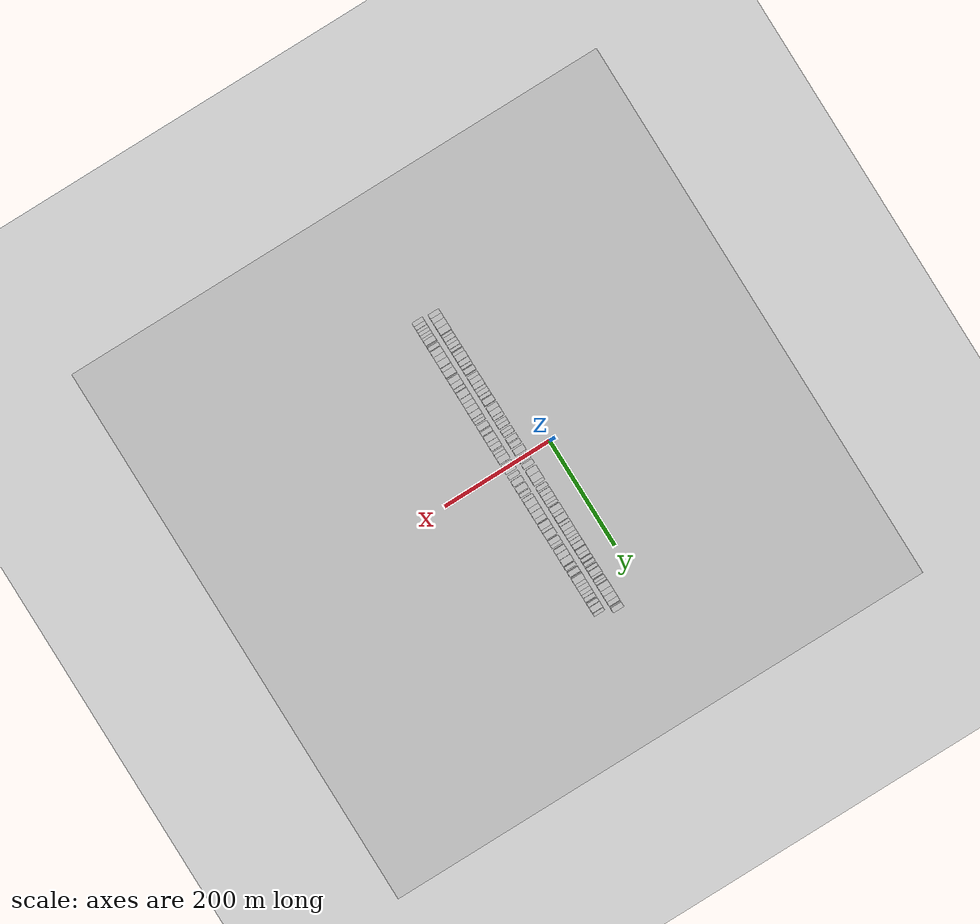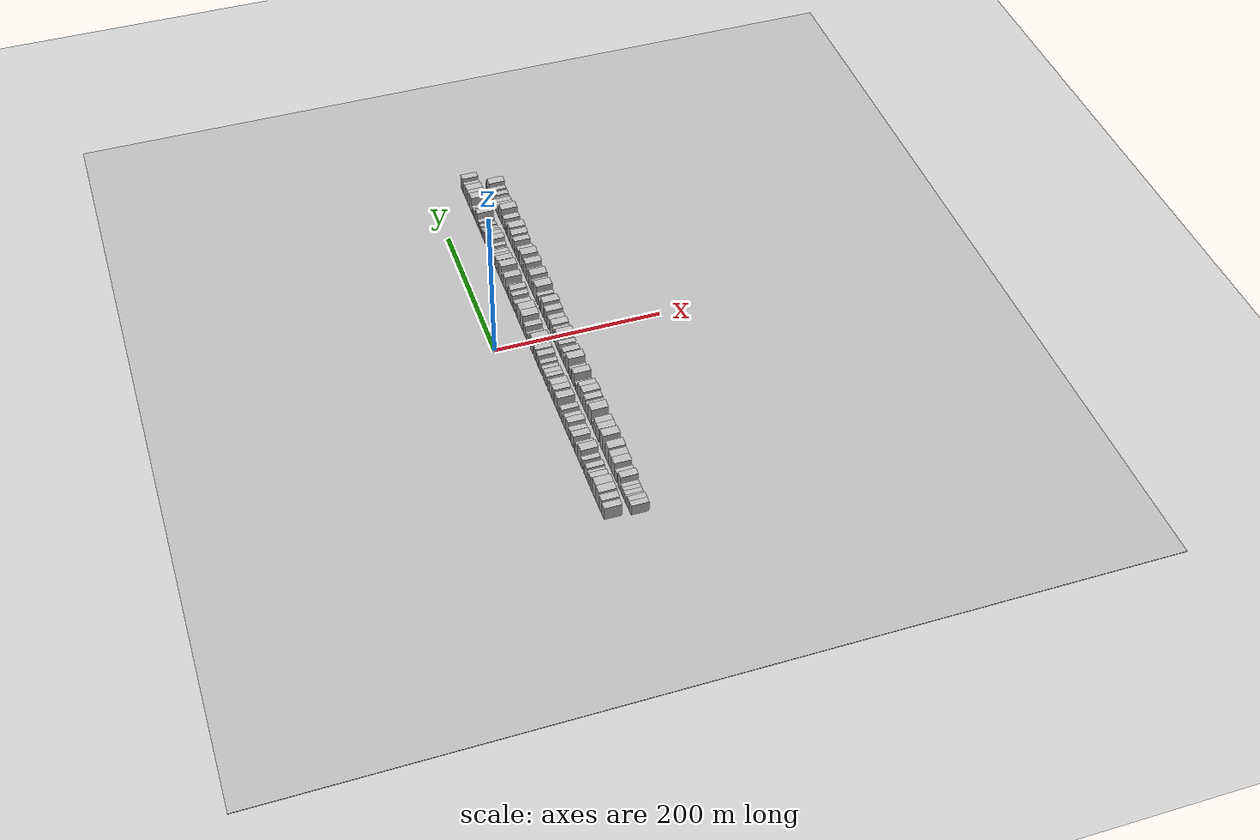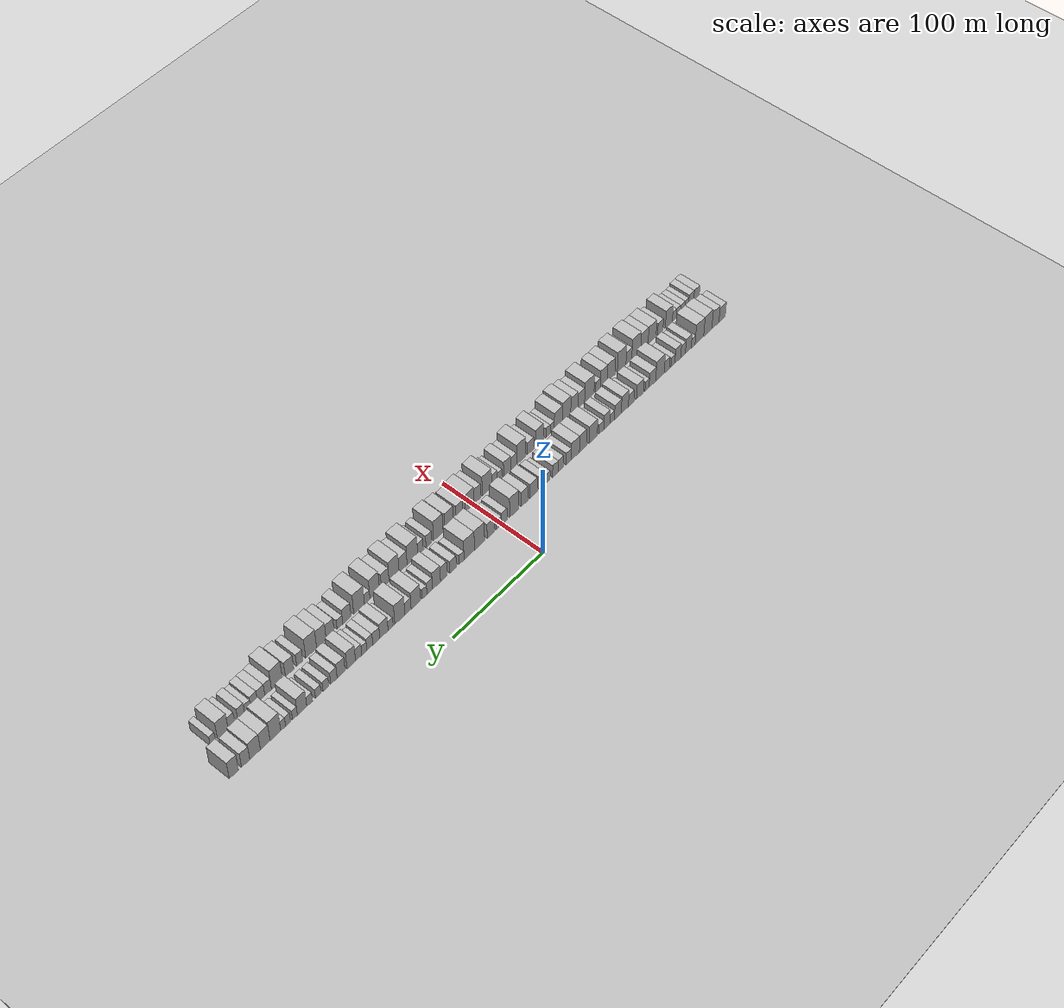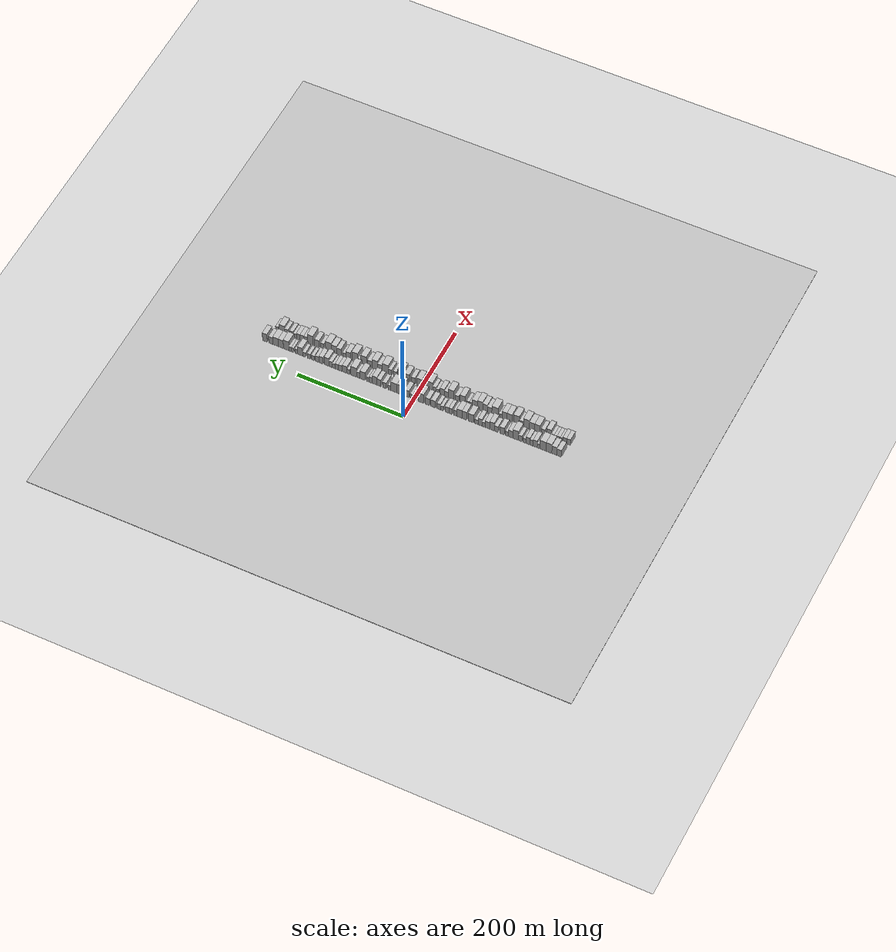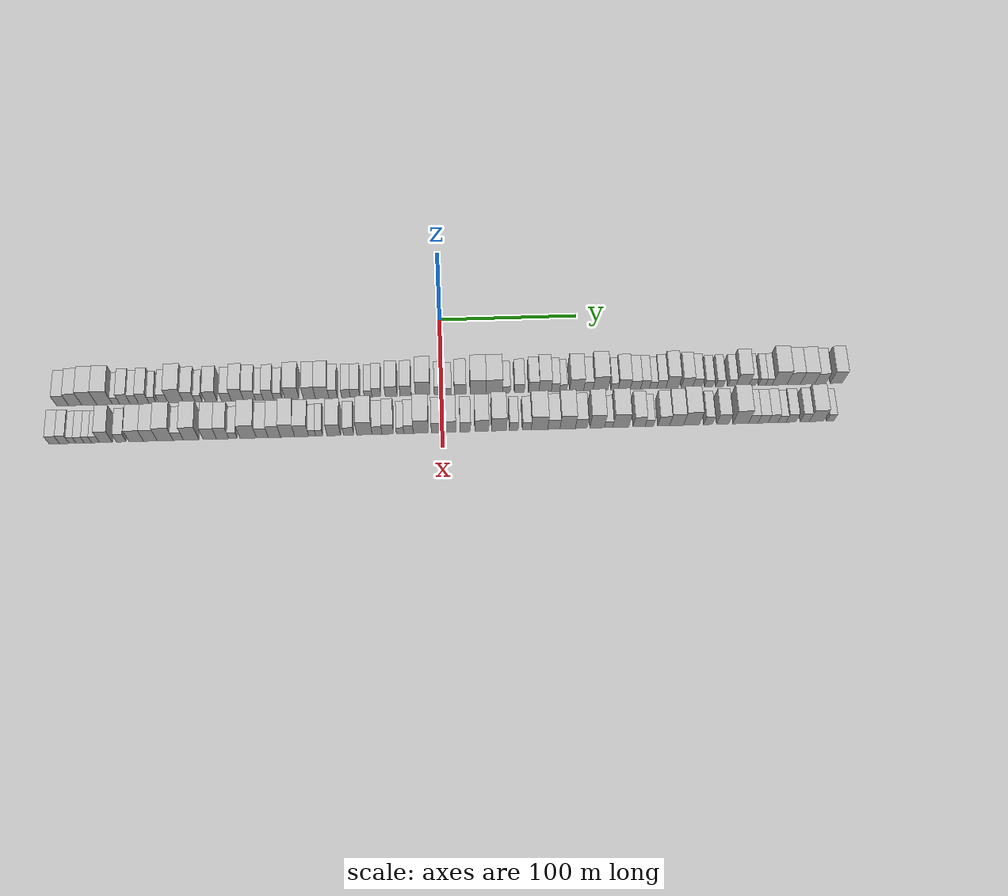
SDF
<?xml version="1.0" encoding="utf-8"?>

<sdf version="1.6">

   <world name="default">

      <gui fullscreen="0">

         <camera name="user_camera">

            <pose>-15 0 4.57585 0 0 0</pose>

            <view_controller>orbit</view_controller>

         </camera>

      </gui>

      <scene>

         <sky>

           <clouds>

             <speed>12</speed>

           </clouds>

         </sky>

         <ambient>0.4 0.4 0.4 1</ambient>

         <background>0.7 0.7 0.7 1</background>

         <shadows>1</shadows>

      </scene>

      <gravity>0 0 -9.8066</gravity>

      <magnetic_field>6e-06 2.3e-05 -4.2e-05</magnetic_field>

      <physics default="0" name="default_physics" type="ode">

         <ode>

            <solver>

               <type>quick</type>

               <iters>10</iters>

               <sor>1.0</sor>

               <use_dynamic_moi_rescaling>0</use_dynamic_moi_rescaling>

            </solver>

            <constraints>

               <cfm>0</cfm>

               <erp>0.2</erp>

               <contact_max_correcting_vel>100</contact_max_correcting_vel>

               <contact_surface_layer>0.001</contact_surface_layer>

            </constraints>

         </ode>

         <max_step_size>0.004</max_step_size>

         <real_time_factor>1</real_time_factor>

         <real_time_update_rate>250</real_time_update_rate>

      </physics>

      <light name="sun" type="directional">

         <cast_shadows>1</cast_shadows>

         <pose>0 0 10 0 0 0</pose>

         <diffuse>0.8 0.8 0.8 1</diffuse>

         <specular>0.2 0.2 0.2 1</specular>

         <attenuation>

            <range>1000</range>

            <constant>0.9</constant>

            <linear>0.01</linear>

            <quadratic>0.001</quadratic>

         </attenuation>

         <direction>-0.5 0.1 -0.9</direction>

      </light>

      <include>

         <name>ground_plane_1</name>

         <uri>model://HANNAS_ground_plane</uri>

         <pose>0 0 0  0 0 0</pose>

      </include>

      <include>

         <name>ground_plane_2</name>

         <uri>model://HANNAS_ground_plane</uri>

         <pose>100 0 0  0 0 0</pose>

      </include>

      <model name="building_1">

         <static>1</static>

         <pose frame="">50.0000 -270.7462 0 0.000000 0.000000 0.000000</pose>

         <link name="link">

            <pose frame="">0 0 9.00 0 0 0</pose>

            <collision name="collision">

               <geometry>

                  <box>

                     <size>20.0000 8.5076 18.0000</size>

                  </box>

               </geometry>

               <max_contacts>10</max_contacts>

               <surface>

                  <contact>

                     <ode/>

                  </contact>

                  <bounce/>

                  <friction>

                     <torsional>

                        <ode/>

                     </torsional>

                     <ode/>

                  </friction>

               </surface>

            </collision>

            <visual name="visual">

               <cast_shadows>0</cast_shadows>

               <geometry>

                  <box>

                     <size>20.0000 8.5076 18.0000</size>

                  </box>

               </geometry>

               <material>

                  <script>

                     <uri>model://HANNAS_wall/materials/scripts</uri>

                     <uri>model://HANNAS_wall/materials/textures</uri>

                     <name>vrc/HANNAS_wall</name>

                  </script>

               </material>

            </visual>

            <self_collide>0</self_collide>

            <enable_wind>0</enable_wind>

            <kinematic>0</kinematic>

         </link>

      </model>

      <model name="building_2">

         <static>1</static>

         <pose frame="">50.0000 -261.8234 0 0.000000 0.000000 0.000000</pose>

         <link name="link">

            <pose frame="">0 0 10.50 0 0 0</pose>

            <collision name="collision">

               <geometry>

                  <box>

                     <size>20.0000 9.3380 21.0000</size>

                  </box>

               </geometry>

               <max_contacts>10</max_contacts>

               <surface>

                  <contact>

                     <ode/>

                  </contact>

                  <bounce/>

                  <friction>

                     <torsional>

                        <ode/>

                     </torsional>

                     <ode/>

                  </friction>

               </surface>

            </collision>

            <visual name="visual">

               <cast_shadows>0</cast_shadows>

               <geometry>

                  <box>

                     <size>20.0000 9.3380 21.0000</size>

                  </box>

               </geometry>

               <material>

                  <script>

                     <uri>model://HANNAS_wall/materials/scripts</uri>

                     <uri>model://HANNAS_wall/materials/textures</uri>

                     <name>vrc/HANNAS_wall</name>

                  </script>

               </material>

            </visual>

            <self_collide>0</self_collide>

            <enable_wind>0</enable_wind>

            <kinematic>0</kinematic>

         </link>

      </model>

      <model name="building_3">

         <static>1</static>

         <pose frame="">50.0000 -251.8180 0 0.000000 0.000000 0.000000</pose>

         <link name="link">

            <pose frame="">0 0 12.00 0 0 0</pose>

            <collision name="collision">

               <geometry>

                  <box>

                     <size>20.0000 10.6729 24.0000</size>

                  </box>

               </geometry>

               <max_contacts>10</max_contacts>

               <surface>

                  <contact>

                     <ode/>

                  </contact>

                  <bounce/>

                  <friction>

                     <torsional>

                        <ode/>

                     </torsional>

                     <ode/>

                  </friction>

               </surface>

            </collision>

            <visual name="visual">

               <cast_shadows>0</cast_shadows>

               <geometry>

                  <box>

                     <size>20.0000 10.6729 24.0000</size>

                  </box>

               </geometry>

               <material>

                  <script>

                     <uri>model://HANNAS_wall/materials/scripts</uri>

                     <uri>model://HANNAS_wall/materials/textures</uri>

                     <name>vrc/HANNAS_wall</name>

                  </script>

               </material>

            </visual>

            <self_collide>0</self_collide>

            <enable_wind>0</enable_wind>

            <kinematic>0</kinematic>

         </link>

      </model>

      <model name="building_4">

         <static>1</static>

         <pose frame="">50.0000 -240.9079 0 0.000000 0.000000 0.000000</pose>

         <link name="link">

            <pose frame="">0 0 12.00 0 0 0</pose>

            <collision name="collision">

               <geometry>

                  <box>

                     <size>20.0000 11.1472 24.0000</size>

                  </box>

               </geometry>

               <max_contacts>10</max_contacts>

               <surface>

                  <contact>

                     <ode/>

                  </contact>

                  <bounce/>

                  <friction>

                     <torsional>

                        <ode/>

                     </torsional>

                     <ode/>

                  </friction>

               </surface>

            </collision>

            <visual name="visual">

               <cast_shadows>0</cast_shadows>

               <geometry>

                  <box>

                     <size>20.0000 11.1472 24.0000</size>

                  </box>

               </geometry>

               <material>

                  <script>

                     <uri>model://HANNAS_wall/materials/scripts</uri>

                     <uri>model://HANNAS_wall/materials/textures</uri>

                     <name>vrc/HANNAS_wall</name>

                  </script>

               </material>

            </visual>

            <self_collide>0</self_collide>

            <enable_wind>0</enable_wind>

            <kinematic>0</kinematic>

         </link>

      </model>

      <model name="building_5">

         <static>1</static>

         <pose frame="">50.0000 -232.7691 0 0.000000 0.000000 0.000000</pose>

         <link name="link">

            <pose frame="">0 0 6.00 0 0 0</pose>

            <collision name="collision">

               <geometry>

                  <box>

                     <size>20.0000 5.1303 12.0000</size>

                  </box>

               </geometry>

               <max_contacts>10</max_contacts>

               <surface>

                  <contact>

                     <ode/>

                  </contact>

                  <bounce/>

                  <friction>

                     <torsional>

                        <ode/>

                     </torsional>

                     <ode/>

                  </friction>

               </surface>

            </collision>

            <visual name="visual">

               <cast_shadows>0</cast_shadows>

               <geometry>

                  <box>

                     <size>20.0000 5.1303 12.0000</size>

                  </box>

               </geometry>

               <material>

                  <script>

                     <uri>model://HANNAS_wall/materials/scripts</uri>

                     <uri>model://HANNAS_wall/materials/textures</uri>

                     <name>vrc/HANNAS_wall</name>

                  </script>

               </material>

            </visual>

            <self_collide>0</self_collide>

            <enable_wind>0</enable_wind>

            <kinematic>0</kinematic>

         </link>

      </model>

      <model name="building_6">

         <static>1</static>

         <pose frame="">50.0000 -226.4638 0 0.000000 0.000000 0.000000</pose>

         <link name="link">

            <pose frame="">0 0 9.00 0 0 0</pose>

            <collision name="collision">

               <geometry>

                  <box>

                     <size>20.0000 7.4803 18.0000</size>

                  </box>

               </geometry>

               <max_contacts>10</max_contacts>

               <surface>

                  <contact>

                     <ode/>

                  </contact>

                  <bounce/>

                  <friction>

                     <torsional>

                        <ode/>

                     </torsional>

                     <ode/>

                  </friction>

               </surface>

            </collision>

            <visual name="visual">

               <cast_shadows>0</cast_shadows>

               <geometry>

                  <box>

                     <size>20.0000 7.4803 18.0000</size>

                  </box>

               </geometry>

               <material>

                  <script>

                     <uri>model://HANNAS_wall/materials/scripts</uri>

                     <uri>model://HANNAS_wall/materials/textures</uri>

                     <name>vrc/HANNAS_wall</name>

                  </script>

               </material>

            </visual>

            <self_collide>0</self_collide>

            <enable_wind>0</enable_wind>

            <kinematic>0</kinematic>

         </link>

      </model>

      <model name="building_7">

         <static>1</static>

         <pose frame="">50.0000 -219.6944 0 0.000000 0.000000 0.000000</pose>

         <link name="link">

            <pose frame="">0 0 7.50 0 0 0</pose>

            <collision name="collision">

               <geometry>

                  <box>

                     <size>20.0000 6.0585 15.0000</size>

                  </box>

               </geometry>

               <max_contacts>10</max_contacts>

               <surface>

                  <contact>

                     <ode/>

                  </contact>

                  <bounce/>

                  <friction>

                     <torsional>

                        <ode/>

                     </torsional>

                     <ode/>

                  </friction>

               </surface>

            </collision>

            <visual name="visual">

               <cast_shadows>0</cast_shadows>

               <geometry>

                  <box>

                     <size>20.0000 6.0585 15.0000</size>

                  </box>

               </geometry>

               <material>

                  <script>

                     <uri>model://HANNAS_wall/materials/scripts</uri>

                     <uri>model://HANNAS_wall/materials/textures</uri>

                     <name>vrc/HANNAS_wall</name>

                  </script>

               </material>

            </visual>

            <self_collide>0</self_collide>

            <enable_wind>0</enable_wind>

            <kinematic>0</kinematic>

         </link>

      </model>

      <model name="building_8">

         <static>1</static>

         <pose frame="">50.0000 -212.9263 0 0.000000 0.000000 0.000000</pose>

         <link name="link">

            <pose frame="">0 0 9.00 0 0 0</pose>

            <collision name="collision">

               <geometry>

                  <box>

                     <size>20.0000 7.4778 18.0000</size>

                  </box>

               </geometry>

               <max_contacts>10</max_contacts>

               <surface>

                  <contact>

                     <ode/>

                  </contact>

                  <bounce/>

                  <friction>

                     <torsional>

                        <ode/>

                     </torsional>

                     <ode/>

                  </friction>

               </surface>

            </collision>

            <visual name="visual">

               <cast_shadows>0</cast_shadows>

               <geometry>

                  <box>

                     <size>20.0000 7.4778 18.0000</size>

                  </box>

               </geometry>

               <material>

                  <script>

                     <uri>model://HANNAS_wall/materials/scripts</uri>

                     <uri>model://HANNAS_wall/materials/textures</uri>

                     <name>vrc/HANNAS_wall</name>

                  </script>

               </material>

            </visual>

            <self_collide>0</self_collide>

            <enable_wind>0</enable_wind>

            <kinematic>0</kinematic>

         </link>

      </model>

      <model name="building_9">

         <static>1</static>

         <pose frame="">50.0000 -206.6918 0 0.000000 0.000000 0.000000</pose>

         <link name="link">

            <pose frame="">0 0 6.00 0 0 0</pose>

            <collision name="collision">

               <geometry>

                  <box>

                     <size>20.0000 4.9912 12.0000</size>

                  </box>

               </geometry>

               <max_contacts>10</max_contacts>

               <surface>

                  <contact>

                     <ode/>

                  </contact>

                  <bounce/>

                  <friction>

                     <torsional>

                        <ode/>

                     </torsional>

                     <ode/>

                  </friction>

               </surface>

            </collision>

            <visual name="visual">

               <cast_shadows>0</cast_shadows>

               <geometry>

                  <box>

                     <size>20.0000 4.9912 12.0000</size>

                  </box>

               </geometry>

               <material>

                  <script>

                     <uri>model://HANNAS_wall/materials/scripts</uri>

                     <uri>model://HANNAS_wall/materials/textures</uri>

                     <name>vrc/HANNAS_wall</name>

                  </script>

               </material>

            </visual>

            <self_collide>0</self_collide>

            <enable_wind>0</enable_wind>

            <kinematic>0</kinematic>

         </link>

      </model>

      <model name="building_10">

         <static>1</static>

         <pose frame="">50.0000 -198.9097 0 0.000000 0.000000 0.000000</pose>

         <link name="link">

            <pose frame="">0 0 7.50 0 0 0</pose>

            <collision name="collision">

               <geometry>

                  <box>

                     <size>20.0000 6.5731 15.0000</size>

                  </box>

               </geometry>

               <max_contacts>10</max_contacts>

               <surface>

                  <contact>

                     <ode/>

                  </contact>

                  <bounce/>

                  <friction>

                     <torsional>

                        <ode/>

                     </torsional>

                     <ode/>

                  </friction>

               </surface>

            </collision>

            <visual name="visual">

               <cast_shadows>0</cast_shadows>

               <geometry>

                  <box>

                     <size>20.0000 6.5731 15.0000</size>

                  </box>

               </geometry>

               <material>

                  <script>

                     <uri>model://HANNAS_wall/materials/scripts</uri>

                     <uri>model://HANNAS_wall/materials/textures</uri>

                     <name>vrc/HANNAS_wall</name>

                  </script>

               </material>

            </visual>

            <self_collide>0</self_collide>

            <enable_wind>0</enable_wind>

            <kinematic>0</kinematic>

         </link>

      </model>

      <model name="building_11">

         <static>1</static>

         <pose frame="">50.0000 -190.1880 0 0.000000 0.000000 0.000000</pose>

         <link name="link">

            <pose frame="">0 0 12.00 0 0 0</pose>

            <collision name="collision">

               <geometry>

                  <box>

                     <size>20.0000 10.8702 24.0000</size>

                  </box>

               </geometry>

               <max_contacts>10</max_contacts>

               <surface>

                  <contact>

                     <ode/>

                  </contact>

                  <bounce/>

                  <friction>

                     <torsional>

                        <ode/>

                     </torsional>

                     <ode/>

                  </friction>

               </surface>

            </collision>

            <visual name="visual">

               <cast_shadows>0</cast_shadows>

               <geometry>

                  <box>

                     <size>20.0000 10.8702 24.0000</size>

                  </box>

               </geometry>

               <material>

                  <script>

                     <uri>model://HANNAS_wall/materials/scripts</uri>

                     <uri>model://HANNAS_wall/materials/textures</uri>

                     <name>vrc/HANNAS_wall</name>

                  </script>

               </material>

            </visual>

            <self_collide>0</self_collide>

            <enable_wind>0</enable_wind>

            <kinematic>0</kinematic>

         </link>

      </model>

      <model name="building_12">

         <static>1</static>

         <pose frame="">50.0000 -180.5997 0 0.000000 0.000000 0.000000</pose>

         <link name="link">

            <pose frame="">0 0 9.00 0 0 0</pose>

            <collision name="collision">

               <geometry>

                  <box>

                     <size>20.0000 8.3064 18.0000</size>

                  </box>

               </geometry>

               <max_contacts>10</max_contacts>

               <surface>

                  <contact>

                     <ode/>

                  </contact>

                  <bounce/>

                  <friction>

                     <torsional>

                        <ode/>

                     </torsional>

                     <ode/>

                  </friction>

               </surface>

            </collision>

            <visual name="visual">

               <cast_shadows>0</cast_shadows>

               <geometry>

                  <box>

                     <size>20.0000 8.3064 18.0000</size>

                  </box>

               </geometry>

               <material>

                  <script>

                     <uri>model://HANNAS_wall/materials/scripts</uri>

                     <uri>model://HANNAS_wall/materials/textures</uri>

                     <name>vrc/HANNAS_wall</name>

                  </script>

               </material>

            </visual>

            <self_collide>0</self_collide>

            <enable_wind>0</enable_wind>

            <kinematic>0</kinematic>

         </link>

      </model>

      <model name="building_13">

         <static>1</static>

         <pose frame="">50.0000 -173.8752 0 0.000000 0.000000 0.000000</pose>

         <link name="link">

            <pose frame="">0 0 6.00 0 0 0</pose>

            <collision name="collision">

               <geometry>

                  <box>

                     <size>20.0000 5.1427 12.0000</size>

                  </box>

               </geometry>

               <max_contacts>10</max_contacts>

               <surface>

                  <contact>

                     <ode/>

                  </contact>

                  <bounce/>

                  <friction>

                     <torsional>

                        <ode/>

                     </torsional>

                     <ode/>

                  </friction>

               </surface>

            </collision>

            <visual name="visual">

               <cast_shadows>0</cast_shadows>

               <geometry>

                  <box>

                     <size>20.0000 5.1427 12.0000</size>

                  </box>

               </geometry>

               <material>

                  <script>

                     <uri>model://HANNAS_wall/materials/scripts</uri>

                     <uri>model://HANNAS_wall/materials/textures</uri>

                     <name>vrc/HANNAS_wall</name>

                  </script>

               </material>

            </visual>

            <self_collide>0</self_collide>

            <enable_wind>0</enable_wind>

            <kinematic>0</kinematic>

         </link>

      </model>

      <model name="building_14">

         <static>1</static>

         <pose frame="">50.0000 -164.9254 0 0.000000 0.000000 0.000000</pose>

         <link name="link">

            <pose frame="">0 0 9.00 0 0 0</pose>

            <collision name="collision">

               <geometry>

                  <box>

                     <size>20.0000 8.7569 18.0000</size>

                  </box>

               </geometry>

               <max_contacts>10</max_contacts>

               <surface>

                  <contact>

                     <ode/>

                  </contact>

                  <bounce/>

                  <friction>

                     <torsional>

                        <ode/>

                     </torsional>

                     <ode/>

                  </friction>

               </surface>

            </collision>

            <visual name="visual">

               <cast_shadows>0</cast_shadows>

               <geometry>

                  <box>

                     <size>20.0000 8.7569 18.0000</size>

                  </box>

               </geometry>

               <material>

                  <script>

                     <uri>model://HANNAS_wall/materials/scripts</uri>

                     <uri>model://HANNAS_wall/materials/textures</uri>

                     <name>vrc/HANNAS_wall</name>

                  </script>

               </material>

            </visual>

            <self_collide>0</self_collide>

            <enable_wind>0</enable_wind>

            <kinematic>0</kinematic>

         </link>

      </model>

      <model name="building_15">

         <static>1</static>

         <pose frame="">50.0000 -154.0397 0 0.000000 0.000000 0.000000</pose>

         <link name="link">

            <pose frame="">0 0 7.50 0 0 0</pose>

            <collision name="collision">

               <geometry>

                  <box>

                     <size>20.0000 7.0144 15.0000</size>

                  </box>

               </geometry>

               <max_contacts>10</max_contacts>

               <surface>

                  <contact>

                     <ode/>

                  </contact>

                  <bounce/>

                  <friction>

                     <torsional>

                        <ode/>

                     </torsional>

                     <ode/>

                  </friction>

               </surface>

            </collision>

            <visual name="visual">

               <cast_shadows>0</cast_shadows>

               <geometry>

                  <box>

                     <size>20.0000 7.0144 15.0000</size>

                  </box>

               </geometry>

               <material>

                  <script>

                     <uri>model://HANNAS_wall/materials/scripts</uri>

                     <uri>model://HANNAS_wall/materials/textures</uri>

                     <name>vrc/HANNAS_wall</name>

                  </script>

               </material>

            </visual>

            <self_collide>0</self_collide>

            <enable_wind>0</enable_wind>

            <kinematic>0</kinematic>

         </link>

      </model>

      <model name="building_16">

         <static>1</static>

         <pose frame="">50.0000 -146.1024 0 0.000000 0.000000 0.000000</pose>

         <link name="link">

            <pose frame="">0 0 10.50 0 0 0</pose>

            <collision name="collision">

               <geometry>

                  <box>

                     <size>20.0000 8.8601 21.0000</size>

                  </box>

               </geometry>

               <max_contacts>10</max_contacts>

               <surface>

                  <contact>

                     <ode/>

                  </contact>

                  <bounce/>

                  <friction>

                     <torsional>

                        <ode/>

                     </torsional>

                     <ode/>

                  </friction>

               </surface>

            </collision>

            <visual name="visual">

               <cast_shadows>0</cast_shadows>

               <geometry>

                  <box>

                     <size>20.0000 8.8601 21.0000</size>

                  </box>

               </geometry>

               <material>

                  <script>

                     <uri>model://HANNAS_wall/materials/scripts</uri>

                     <uri>model://HANNAS_wall/materials/textures</uri>

                     <name>vrc/HANNAS_wall</name>

                  </script>

               </material>

            </visual>

            <self_collide>0</self_collide>

            <enable_wind>0</enable_wind>

            <kinematic>0</kinematic>

         </link>

      </model>

      <model name="building_17">

         <static>1</static>

         <pose frame="">50.0000 -137.4521 0 0.000000 0.000000 0.000000</pose>

         <link name="link">

            <pose frame="">0 0 9.00 0 0 0</pose>

            <collision name="collision">

               <geometry>

                  <box>

                     <size>20.0000 8.4406 18.0000</size>

                  </box>

               </geometry>

               <max_contacts>10</max_contacts>

               <surface>

                  <contact>

                     <ode/>

                  </contact>

                  <bounce/>

                  <friction>

                     <torsional>

                        <ode/>

                     </torsional>

                     <ode/>

                  </friction>

               </surface>

            </collision>

            <visual name="visual">

               <cast_shadows>0</cast_shadows>

               <geometry>

                  <box>

                     <size>20.0000 8.4406 18.0000</size>

                  </box>

               </geometry>

               <material>

                  <script>

                     <uri>model://HANNAS_wall/materials/scripts</uri>

                     <uri>model://HANNAS_wall/materials/textures</uri>

                     <name>vrc/HANNAS_wall</name>

                  </script>

               </material>

            </visual>

            <self_collide>0</self_collide>

            <enable_wind>0</enable_wind>

            <kinematic>0</kinematic>

         </link>

      </model>

      <model name="building_18">

         <static>1</static>

         <pose frame="">50.0000 -130.4645 0 0.000000 0.000000 0.000000</pose>

         <link name="link">

            <pose frame="">0 0 6.00 0 0 0</pose>

            <collision name="collision">

               <geometry>

                  <box>

                     <size>20.0000 5.5346 12.0000</size>

                  </box>

               </geometry>

               <max_contacts>10</max_contacts>

               <surface>

                  <contact>

                     <ode/>

                  </contact>

                  <bounce/>

                  <friction>

                     <torsional>

                        <ode/>

                     </torsional>

                     <ode/>

                  </friction>

               </surface>

            </collision>

            <visual name="visual">

               <cast_shadows>0</cast_shadows>

               <geometry>

                  <box>

                     <size>20.0000 5.5346 12.0000</size>

                  </box>

               </geometry>

               <material>

                  <script>

                     <uri>model://HANNAS_wall/materials/scripts</uri>

                     <uri>model://HANNAS_wall/materials/textures</uri>

                     <name>vrc/HANNAS_wall</name>

                  </script>

               </material>

            </visual>

            <self_collide>0</self_collide>

            <enable_wind>0</enable_wind>

            <kinematic>0</kinematic>

         </link>

      </model>

      <model name="building_19">

         <static>1</static>

         <pose frame="">50.0000 -123.9493 0 0.000000 0.000000 0.000000</pose>

         <link name="link">

            <pose frame="">0 0 9.00 0 0 0</pose>

            <collision name="collision">

               <geometry>

                  <box>

                     <size>20.0000 7.4958 18.0000</size>

                  </box>

               </geometry>

               <max_contacts>10</max_contacts>

               <surface>

                  <contact>

                     <ode/>

                  </contact>

                  <bounce/>

                  <friction>

                     <torsional>

                        <ode/>

                     </torsional>

                     <ode/>

                  </friction>

               </surface>

            </collision>

            <visual name="visual">

               <cast_shadows>0</cast_shadows>

               <geometry>

                  <box>

                     <size>20.0000 7.4958 18.0000</size>

                  </box>

               </geometry>

               <material>

                  <script>

                     <uri>model://HANNAS_wall/materials/scripts</uri>

                     <uri>model://HANNAS_wall/materials/textures</uri>

                     <name>vrc/HANNAS_wall</name>

                  </script>

               </material>

            </visual>

            <self_collide>0</self_collide>

            <enable_wind>0</enable_wind>

            <kinematic>0</kinematic>

         </link>

      </model>

      <model name="building_20">

         <static>1</static>

         <pose frame="">50.0000 -117.2490 0 0.000000 0.000000 0.000000</pose>

         <link name="link">

            <pose frame="">0 0 6.00 0 0 0</pose>

            <collision name="collision">

               <geometry>

                  <box>

                     <size>20.0000 5.9047 12.0000</size>

                  </box>

               </geometry>

               <max_contacts>10</max_contacts>

               <surface>

                  <contact>

                     <ode/>

                  </contact>

                  <bounce/>

                  <friction>

                     <torsional>

                        <ode/>

                     </torsional>

                     <ode/>

                  </friction>

               </surface>

            </collision>

            <visual name="visual">

               <cast_shadows>0</cast_shadows>

               <geometry>

                  <box>

                     <size>20.0000 5.9047 12.0000</size>

                  </box>

               </geometry>

               <material>

                  <script>

                     <uri>model://HANNAS_wall/materials/scripts</uri>

                     <uri>model://HANNAS_wall/materials/textures</uri>

                     <name>vrc/HANNAS_wall</name>

                  </script>

               </material>

            </visual>

            <self_collide>0</self_collide>

            <enable_wind>0</enable_wind>

            <kinematic>0</kinematic>

         </link>

      </model>

      <model name="building_21">

         <static>1</static>

         <pose frame="">50.0000 -107.1935 0 0.000000 0.000000 0.000000</pose>

         <link name="link">

            <pose frame="">0 0 10.50 0 0 0</pose>

            <collision name="collision">

               <geometry>

                  <box>

                     <size>20.0000 10.2065 21.0000</size>

                  </box>

               </geometry>

               <max_contacts>10</max_contacts>

               <surface>

                  <contact>

                     <ode/>

                  </contact>

                  <bounce/>

                  <friction>

                     <torsional>

                        <ode/>

                     </torsional>

                     <ode/>

                  </friction>

               </surface>

            </collision>

            <visual name="visual">

               <cast_shadows>0</cast_shadows>

               <geometry>

                  <box>

                     <size>20.0000 10.2065 21.0000</size>

                  </box>

               </geometry>

               <material>

                  <script>

                     <uri>model://HANNAS_wall/materials/scripts</uri>

                     <uri>model://HANNAS_wall/materials/textures</uri>

                     <name>vrc/HANNAS_wall</name>

                  </script>

               </material>

            </visual>

            <self_collide>0</self_collide>

            <enable_wind>0</enable_wind>

            <kinematic>0</kinematic>

         </link>

      </model>

      <model name="building_22">

         <static>1</static>

         <pose frame="">50.0000 -94.8351 0 0.000000 0.000000 0.000000</pose>

         <link name="link">

            <pose frame="">0 0 10.50 0 0 0</pose>

            <collision name="collision">

               <geometry>

                  <box>

                     <size>20.0000 8.5103 21.0000</size>

                  </box>

               </geometry>

               <max_contacts>10</max_contacts>

               <surface>

                  <contact>

                     <ode/>

                  </contact>

                  <bounce/>

                  <friction>

                     <torsional>

                        <ode/>

                     </torsional>

                     <ode/>

                  </friction>

               </surface>

            </collision>

            <visual name="visual">

               <cast_shadows>0</cast_shadows>

               <geometry>

                  <box>

                     <size>20.0000 8.5103 21.0000</size>

                  </box>

               </geometry>

               <material>

                  <script>

                     <uri>model://HANNAS_wall/materials/scripts</uri>

                     <uri>model://HANNAS_wall/materials/textures</uri>

                     <name>vrc/HANNAS_wall</name>

                  </script>

               </material>

            </visual>

            <self_collide>0</self_collide>

            <enable_wind>0</enable_wind>

            <kinematic>0</kinematic>

         </link>

      </model>

      <model name="building_23">

         <static>1</static>

         <pose frame="">50.0000 -85.7295 0 0.000000 0.000000 0.000000</pose>

         <link name="link">

            <pose frame="">0 0 10.50 0 0 0</pose>

            <collision name="collision">

               <geometry>

                  <box>

                     <size>20.0000 9.7010 21.0000</size>

                  </box>

               </geometry>

               <max_contacts>10</max_contacts>

               <surface>

                  <contact>

                     <ode/>

                  </contact>

                  <bounce/>

                  <friction>

                     <torsional>

                        <ode/>

                     </torsional>

                     <ode/>

                  </friction>

               </surface>

            </collision>

            <visual name="visual">

               <cast_shadows>0</cast_shadows>

               <geometry>

                  <box>

                     <size>20.0000 9.7010 21.0000</size>

                  </box>

               </geometry>

               <material>

                  <script>

                     <uri>model://HANNAS_wall/materials/scripts</uri>

                     <uri>model://HANNAS_wall/materials/textures</uri>

                     <name>vrc/HANNAS_wall</name>

                  </script>

               </material>

            </visual>

            <self_collide>0</self_collide>

            <enable_wind>0</enable_wind>

            <kinematic>0</kinematic>

         </link>

      </model>

      <model name="building_24">

         <static>1</static>

         <pose frame="">50.0000 -77.7669 0 0.000000 0.000000 0.000000</pose>

         <link name="link">

            <pose frame="">0 0 7.50 0 0 0</pose>

            <collision name="collision">

               <geometry>

                  <box>

                     <size>20.0000 6.2241 15.0000</size>

                  </box>

               </geometry>

               <max_contacts>10</max_contacts>

               <surface>

                  <contact>

                     <ode/>

                  </contact>

                  <bounce/>

                  <friction>

                     <torsional>

                        <ode/>

                     </torsional>

                     <ode/>

                  </friction>

               </surface>

            </collision>

            <visual name="visual">

               <cast_shadows>0</cast_shadows>

               <geometry>

                  <box>

                     <size>20.0000 6.2241 15.0000</size>

                  </box>

               </geometry>

               <material>

                  <script>

                     <uri>model://HANNAS_wall/materials/scripts</uri>

                     <uri>model://HANNAS_wall/materials/textures</uri>

                     <name>vrc/HANNAS_wall</name>

                  </script>

               </material>

            </visual>

            <self_collide>0</self_collide>

            <enable_wind>0</enable_wind>

            <kinematic>0</kinematic>

         </link>

      </model>

      <model name="building_25">

         <static>1</static>

         <pose frame="">50.0000 -68.5766 0 0.000000 0.000000 0.000000</pose>

         <link name="link">

            <pose frame="">0 0 7.50 0 0 0</pose>

            <collision name="collision">

               <geometry>

                  <box>

                     <size>20.0000 6.1565 15.0000</size>

                  </box>

               </geometry>

               <max_contacts>10</max_contacts>

               <surface>

                  <contact>

                     <ode/>

                  </contact>

                  <bounce/>

                  <friction>

                     <torsional>

                        <ode/>

                     </torsional>

                     <ode/>

                  </friction>

               </surface>

            </collision>

            <visual name="visual">

               <cast_shadows>0</cast_shadows>

               <geometry>

                  <box>

                     <size>20.0000 6.1565 15.0000</size>

                  </box>

               </geometry>

               <material>

                  <script>

                     <uri>model://HANNAS_wall/materials/scripts</uri>

                     <uri>model://HANNAS_wall/materials/textures</uri>

                     <name>vrc/HANNAS_wall</name>

                  </script>

               </material>

            </visual>

            <self_collide>0</self_collide>

            <enable_wind>0</enable_wind>

            <kinematic>0</kinematic>

         </link>

      </model>

      <model name="building_26">

         <static>1</static>

         <pose frame="">50.0000 -62.0209 0 0.000000 0.000000 0.000000</pose>

         <link name="link">

            <pose frame="">0 0 7.50 0 0 0</pose>

            <collision name="collision">

               <geometry>

                  <box>

                     <size>20.0000 6.9550 15.0000</size>

                  </box>

               </geometry>

               <max_contacts>10</max_contacts>

               <surface>

                  <contact>

                     <ode/>

                  </contact>

                  <bounce/>

                  <friction>

                     <torsional>

                        <ode/>

                     </torsional>

                     <ode/>

                  </friction>

               </surface>

            </collision>

            <visual name="visual">

               <cast_shadows>0</cast_shadows>

               <geometry>

                  <box>

                     <size>20.0000 6.9550 15.0000</size>

                  </box>

               </geometry>

               <material>

                  <script>

                     <uri>model://HANNAS_wall/materials/scripts</uri>

                     <uri>model://HANNAS_wall/materials/textures</uri>

                     <name>vrc/HANNAS_wall</name>

                  </script>

               </material>

            </visual>

            <self_collide>0</self_collide>

            <enable_wind>0</enable_wind>

            <kinematic>0</kinematic>

         </link>

      </model>

      <model name="building_27">

         <static>1</static>

         <pose frame="">50.0000 -52.7724 0 0.000000 0.000000 0.000000</pose>

         <link name="link">

            <pose frame="">0 0 6.00 0 0 0</pose>

            <collision name="collision">

               <geometry>

                  <box>

                     <size>20.0000 5.5420 12.0000</size>

                  </box>

               </geometry>

               <max_contacts>10</max_contacts>

               <surface>

                  <contact>

                     <ode/>

                  </contact>

                  <bounce/>

                  <friction>

                     <torsional>

                        <ode/>

                     </torsional>

                     <ode/>

                  </friction>

               </surface>

            </collision>

            <visual name="visual">

               <cast_shadows>0</cast_shadows>

               <geometry>

                  <box>

                     <size>20.0000 5.5420 12.0000</size>

                  </box>

               </geometry>

               <material>

                  <script>

                     <uri>model://HANNAS_wall/materials/scripts</uri>

                     <uri>model://HANNAS_wall/materials/textures</uri>

                     <name>vrc/HANNAS_wall</name>

                  </script>

               </material>

            </visual>

            <self_collide>0</self_collide>

            <enable_wind>0</enable_wind>

            <kinematic>0</kinematic>

         </link>

      </model>

      <model name="building_28">

         <static>1</static>

         <pose frame="">50.0000 -46.7659 0 0.000000 0.000000 0.000000</pose>

         <link name="link">

            <pose frame="">0 0 7.50 0 0 0</pose>

            <collision name="collision">

               <geometry>

                  <box>

                     <size>20.0000 6.4709 15.0000</size>

                  </box>

               </geometry>

               <max_contacts>10</max_contacts>

               <surface>

                  <contact>

                     <ode/>

                  </contact>

                  <bounce/>

                  <friction>

                     <torsional>

                        <ode/>

                     </torsional>

                     <ode/>

                  </friction>

               </surface>

            </collision>

            <visual name="visual">

               <cast_shadows>0</cast_shadows>

               <geometry>

                  <box>

                     <size>20.0000 6.4709 15.0000</size>

                  </box>

               </geometry>

               <material>

                  <script>

                     <uri>model://HANNAS_wall/materials/scripts</uri>

                     <uri>model://HANNAS_wall/materials/textures</uri>

                     <name>vrc/HANNAS_wall</name>

                  </script>

               </material>

            </visual>

            <self_collide>0</self_collide>

            <enable_wind>0</enable_wind>

            <kinematic>0</kinematic>

         </link>

      </model>

      <model name="building_29">

         <static>1</static>

         <pose frame="">50.0000 -36.2263 0 0.000000 0.000000 0.000000</pose>

         <link name="link">

            <pose frame="">0 0 9.00 0 0 0</pose>

            <collision name="collision">

               <geometry>

                  <box>

                     <size>20.0000 8.6084 18.0000</size>

                  </box>

               </geometry>

               <max_contacts>10</max_contacts>

               <surface>

                  <contact>

                     <ode/>

                  </contact>

                  <bounce/>

                  <friction>

                     <torsional>

                        <ode/>

                     </torsional>

                     <ode/>

                  </friction>

               </surface>

            </collision>

            <visual name="visual">

               <cast_shadows>0</cast_shadows>

               <geometry>

                  <box>

                     <size>20.0000 8.6084 18.0000</size>

                  </box>

               </geometry>

               <material>

                  <script>

                     <uri>model://HANNAS_wall/materials/scripts</uri>

                     <uri>model://HANNAS_wall/materials/textures</uri>

                     <name>vrc/HANNAS_wall</name>

                  </script>

               </material>

            </visual>

            <self_collide>0</self_collide>

            <enable_wind>0</enable_wind>

            <kinematic>0</kinematic>

         </link>

      </model>

      <model name="building_30">

         <static>1</static>

         <pose frame="">50.0000 -25.9120 0 0.000000 0.000000 0.000000</pose>

         <link name="link">

            <pose frame="">0 0 9.00 0 0 0</pose>

            <collision name="collision">

               <geometry>

                  <box>

                     <size>20.0000 8.0202 18.0000</size>

                  </box>

               </geometry>

               <max_contacts>10</max_contacts>

               <surface>

                  <contact>

                     <ode/>

                  </contact>

                  <bounce/>

                  <friction>

                     <torsional>

                        <ode/>

                     </torsional>

                     <ode/>

                  </friction>

               </surface>

            </collision>

            <visual name="visual">

               <cast_shadows>0</cast_shadows>

               <geometry>

                  <box>

                     <size>20.0000 8.0202 18.0000</size>

                  </box>

               </geometry>

               <material>

                  <script>

                     <uri>model://HANNAS_wall/materials/scripts</uri>

                     <uri>model://HANNAS_wall/materials/textures</uri>

                     <name>vrc/HANNAS_wall</name>

                  </script>

               </material>

            </visual>

            <self_collide>0</self_collide>

            <enable_wind>0</enable_wind>

            <kinematic>0</kinematic>

         </link>

      </model>

      <model name="building_31">

         <static>1</static>

         <pose frame="">50.0000 -13.6503 0 0.000000 0.000000 0.000000</pose>

         <link name="link">

            <pose frame="">0 0 12.00 0 0 0</pose>

            <collision name="collision">

               <geometry>

                  <box>

                     <size>20.0000 10.5032 24.0000</size>

                  </box>

               </geometry>

               <max_contacts>10</max_contacts>

               <surface>

                  <contact>

                     <ode/>

                  </contact>

                  <bounce/>

                  <friction>

                     <torsional>

                        <ode/>

                     </torsional>

                     <ode/>

                  </friction>

               </surface>

            </collision>

            <visual name="visual">

               <cast_shadows>0</cast_shadows>

               <geometry>

                  <box>

                     <size>20.0000 10.5032 24.0000</size>

                  </box>

               </geometry>

               <material>

                  <script>

                     <uri>model://HANNAS_wall/materials/scripts</uri>

                     <uri>model://HANNAS_wall/materials/textures</uri>

                     <name>vrc/HANNAS_wall</name>

                  </script>

               </material>

            </visual>

            <self_collide>0</self_collide>

            <enable_wind>0</enable_wind>

            <kinematic>0</kinematic>

         </link>

      </model>

      <model name="building_32">

         <static>1</static>

         <pose frame="">50.0000 -2.2336 0 0.000000 0.000000 0.000000</pose>

         <link name="link">

            <pose frame="">0 0 7.50 0 0 0</pose>

            <collision name="collision">

               <geometry>

                  <box>

                     <size>20.0000 6.3303 15.0000</size>

                  </box>

               </geometry>

               <max_contacts>10</max_contacts>

               <surface>

                  <contact>

                     <ode/>

                  </contact>

                  <bounce/>

                  <friction>

                     <torsional>

                        <ode/>

                     </torsional>

                     <ode/>

                  </friction>

               </surface>

            </collision>

            <visual name="visual">

               <cast_shadows>0</cast_shadows>

               <geometry>

                  <box>

                     <size>20.0000 6.3303 15.0000</size>

                  </box>

               </geometry>

               <material>

                  <script>

                     <uri>model://HANNAS_wall/materials/scripts</uri>

                     <uri>model://HANNAS_wall/materials/textures</uri>

                     <name>vrc/HANNAS_wall</name>

                  </script>

               </material>

            </visual>

            <self_collide>0</self_collide>

            <enable_wind>0</enable_wind>

            <kinematic>0</kinematic>

         </link>

      </model>

      <model name="building_33">

         <static>1</static>

         <pose frame="">50.0000 3.9265 0 0.000000 0.000000 0.000000</pose>

         <link name="link">

            <pose frame="">0 0 6.00 0 0 0</pose>

            <collision name="collision">

               <geometry>

                  <box>

                     <size>20.0000 5.9898 12.0000</size>

                  </box>

               </geometry>

               <max_contacts>10</max_contacts>

               <surface>

                  <contact>

                     <ode/>

                  </contact>

                  <bounce/>

                  <friction>

                     <torsional>

                        <ode/>

                     </torsional>

                     <ode/>

                  </friction>

               </surface>

            </collision>

            <visual name="visual">

               <cast_shadows>0</cast_shadows>

               <geometry>

                  <box>

                     <size>20.0000 5.9898 12.0000</size>

                  </box>

               </geometry>

               <material>

                  <script>

                     <uri>model://HANNAS_wall/materials/scripts</uri>

                     <uri>model://HANNAS_wall/materials/textures</uri>

                     <name>vrc/HANNAS_wall</name>

                  </script>

               </material>

            </visual>

            <self_collide>0</self_collide>

            <enable_wind>0</enable_wind>

            <kinematic>0</kinematic>

         </link>

      </model>

      <model name="building_34">

         <static>1</static>

         <pose frame="">50.0000 13.1047 0 0.000000 0.000000 0.000000</pose>

         <link name="link">

            <pose frame="">0 0 9.00 0 0 0</pose>

            <collision name="collision">

               <geometry>

                  <box>

                     <size>20.0000 8.3667 18.0000</size>

                  </box>

               </geometry>

               <max_contacts>10</max_contacts>

               <surface>

                  <contact>

                     <ode/>

                  </contact>

                  <bounce/>

                  <friction>

                     <torsional>

                        <ode/>

                     </torsional>

                     <ode/>

                  </friction>

               </surface>

            </collision>

            <visual name="visual">

               <cast_shadows>0</cast_shadows>

               <geometry>

                  <box>

                     <size>20.0000 8.3667 18.0000</size>

                  </box>

               </geometry>

               <material>

                  <script>

                     <uri>model://HANNAS_wall/materials/scripts</uri>

                     <uri>model://HANNAS_wall/materials/textures</uri>

                     <name>vrc/HANNAS_wall</name>

                  </script>

               </material>

            </visual>

            <self_collide>0</self_collide>

            <enable_wind>0</enable_wind>

            <kinematic>0</kinematic>

         </link>

      </model>

      <model name="building_35">

         <static>1</static>

         <pose frame="">50.0000 25.9832 0 0.000000 0.000000 0.000000</pose>

         <link name="link">

            <pose frame="">0 0 12.00 0 0 0</pose>

            <collision name="collision">

               <geometry>

                  <box>

                     <size>20.0000 11.3902 24.0000</size>

                  </box>

               </geometry>

               <max_contacts>10</max_contacts>

               <surface>

                  <contact>

                     <ode/>

                  </contact>

                  <bounce/>

                  <friction>

                     <torsional>

                        <ode/>

                     </torsional>

                     <ode/>

                  </friction>

               </surface>

            </collision>

            <visual name="visual">

               <cast_shadows>0</cast_shadows>

               <geometry>

                  <box>

                     <size>20.0000 11.3902 24.0000</size>

                  </box>

               </geometry>

               <material>

                  <script>

                     <uri>model://HANNAS_wall/materials/scripts</uri>

                     <uri>model://HANNAS_wall/materials/textures</uri>

                     <name>vrc/HANNAS_wall</name>

                  </script>

               </material>

            </visual>

            <self_collide>0</self_collide>

            <enable_wind>0</enable_wind>

            <kinematic>0</kinematic>

         </link>

      </model>

      <model name="building_36">

         <static>1</static>

         <pose frame="">50.0000 37.5372 0 0.000000 0.000000 0.000000</pose>

         <link name="link">

            <pose frame="">0 0 12.00 0 0 0</pose>

            <collision name="collision">

               <geometry>

                  <box>

                     <size>20.0000 11.7177 24.0000</size>

                  </box>

               </geometry>

               <max_contacts>10</max_contacts>

               <surface>

                  <contact>

                     <ode/>

                  </contact>

                  <bounce/>

                  <friction>

                     <torsional>

                        <ode/>

                     </torsional>

                     <ode/>

                  </friction>

               </surface>

            </collision>

            <visual name="visual">

               <cast_shadows>0</cast_shadows>

               <geometry>

                  <box>

                     <size>20.0000 11.7177 24.0000</size>

                  </box>

               </geometry>

               <material>

                  <script>

                     <uri>model://HANNAS_wall/materials/scripts</uri>

                     <uri>model://HANNAS_wall/materials/textures</uri>

                     <name>vrc/HANNAS_wall</name>

                  </script>

               </material>

            </visual>

            <self_collide>0</self_collide>

            <enable_wind>0</enable_wind>

            <kinematic>0</kinematic>

         </link>

      </model>

      <model name="building_37">

         <static>1</static>

         <pose frame="">50.0000 46.2099 0 0.000000 0.000000 0.000000</pose>

         <link name="link">

            <pose frame="">0 0 6.00 0 0 0</pose>

            <collision name="collision">

               <geometry>

                  <box>

                     <size>20.0000 5.6278 12.0000</size>

                  </box>

               </geometry>

               <max_contacts>10</max_contacts>

               <surface>

                  <contact>

                     <ode/>

                  </contact>

                  <bounce/>

                  <friction>

                     <torsional>

                        <ode/>

                     </torsional>

                     <ode/>

                  </friction>

               </surface>

            </collision>

            <visual name="visual">

               <cast_shadows>0</cast_shadows>

               <geometry>

                  <box>

                     <size>20.0000 5.6278 12.0000</size>

                  </box>

               </geometry>

               <material>

                  <script>

                     <uri>model://HANNAS_wall/materials/scripts</uri>

                     <uri>model://HANNAS_wall/materials/textures</uri>

                     <name>vrc/HANNAS_wall</name>

                  </script>

               </material>

            </visual>

            <self_collide>0</self_collide>

            <enable_wind>0</enable_wind>

            <kinematic>0</kinematic>

         </link>

      </model>

      <model name="building_38">

         <static>1</static>

         <pose frame="">50.0000 55.5786 0 0.000000 0.000000 0.000000</pose>

         <link name="link">

            <pose frame="">0 0 7.50 0 0 0</pose>

            <collision name="collision">

               <geometry>

                  <box>

                     <size>20.0000 7.1096 15.0000</size>

                  </box>

               </geometry>

               <max_contacts>10</max_contacts>

               <surface>

                  <contact>

                     <ode/>

                  </contact>

                  <bounce/>

                  <friction>

                     <torsional>

                        <ode/>

                     </torsional>

                     <ode/>

                  </friction>

               </surface>

            </collision>

            <visual name="visual">

               <cast_shadows>0</cast_shadows>

               <geometry>

                  <box>

                     <size>20.0000 7.1096 15.0000</size>

                  </box>

               </geometry>

               <material>

                  <script>

                     <uri>model://HANNAS_wall/materials/scripts</uri>

                     <uri>model://HANNAS_wall/materials/textures</uri>

                     <name>vrc/HANNAS_wall</name>

                  </script>

               </material>

            </visual>

            <self_collide>0</self_collide>

            <enable_wind>0</enable_wind>

            <kinematic>0</kinematic>

         </link>

      </model>

      <model name="building_39">

         <static>1</static>

         <pose frame="">50.0000 65.8306 0 0.000000 0.000000 0.000000</pose>

         <link name="link">

            <pose frame="">0 0 9.00 0 0 0</pose>

            <collision name="collision">

               <geometry>

                  <box>

                     <size>20.0000 7.3943 18.0000</size>

                  </box>

               </geometry>

               <max_contacts>10</max_contacts>

               <surface>

                  <contact>

                     <ode/>

                  </contact>

                  <bounce/>

                  <friction>

                     <torsional>

                        <ode/>

                     </torsional>

                     <ode/>

                  </friction>

               </surface>

            </collision>

            <visual name="visual">

               <cast_shadows>0</cast_shadows>

               <geometry>

                  <box>

                     <size>20.0000 7.3943 18.0000</size>

                  </box>

               </geometry>

               <material>

                  <script>

                     <uri>model://HANNAS_wall/materials/scripts</uri>

                     <uri>model://HANNAS_wall/materials/textures</uri>

                     <name>vrc/HANNAS_wall</name>

                  </script>

               </material>

            </visual>

            <self_collide>0</self_collide>

            <enable_wind>0</enable_wind>

            <kinematic>0</kinematic>

         </link>

      </model>

      <model name="building_40">

         <static>1</static>

         <pose frame="">50.0000 73.9746 0 0.000000 0.000000 0.000000</pose>

         <link name="link">

            <pose frame="">0 0 10.50 0 0 0</pose>

            <collision name="collision">

               <geometry>

                  <box>

                     <size>20.0000 8.8938 21.0000</size>

                  </box>

               </geometry>

               <max_contacts>10</max_contacts>

               <surface>

                  <contact>

                     <ode/>

                  </contact>

                  <bounce/>

                  <friction>

                     <torsional>

                        <ode/>

                     </torsional>

                     <ode/>

                  </friction>

               </surface>

            </collision>

            <visual name="visual">

               <cast_shadows>0</cast_shadows>

               <geometry>

                  <box>

                     <size>20.0000 8.8938 21.0000</size>

                  </box>

               </geometry>

               <material>

                  <script>

                     <uri>model://HANNAS_wall/materials/scripts</uri>

                     <uri>model://HANNAS_wall/materials/textures</uri>

                     <name>vrc/HANNAS_wall</name>

                  </script>

               </material>

            </visual>

            <self_collide>0</self_collide>

            <enable_wind>0</enable_wind>

            <kinematic>0</kinematic>

         </link>

      </model>

      <model name="building_41">

         <static>1</static>

         <pose frame="">50.0000 81.4546 0 0.000000 0.000000 0.000000</pose>

         <link name="link">

            <pose frame="">0 0 7.50 0 0 0</pose>

            <collision name="collision">

               <geometry>

                  <box>

                     <size>20.0000 6.0662 15.0000</size>

                  </box>

               </geometry>

               <max_contacts>10</max_contacts>

               <surface>

                  <contact>

                     <ode/>

                  </contact>

                  <bounce/>

                  <friction>

                     <torsional>

                        <ode/>

                     </torsional>

                     <ode/>

                  </friction>

               </surface>

            </collision>

            <visual name="visual">

               <cast_shadows>0</cast_shadows>

               <geometry>

                  <box>

                     <size>20.0000 6.0662 15.0000</size>

                  </box>

               </geometry>

               <material>

                  <script>

                     <uri>model://HANNAS_wall/materials/scripts</uri>

                     <uri>model://HANNAS_wall/materials/textures</uri>

                     <name>vrc/HANNAS_wall</name>

                  </script>

               </material>

            </visual>

            <self_collide>0</self_collide>

            <enable_wind>0</enable_wind>

            <kinematic>0</kinematic>

         </link>

      </model>

      <model name="building_42">

         <static>1</static>

         <pose frame="">50.0000 87.0253 0 0.000000 0.000000 0.000000</pose>

         <link name="link">

            <pose frame="">0 0 6.00 0 0 0</pose>

            <collision name="collision">

               <geometry>

                  <box>

                     <size>20.0000 5.0752 12.0000</size>

                  </box>

               </geometry>

               <max_contacts>10</max_contacts>

               <surface>

                  <contact>

                     <ode/>

                  </contact>

                  <bounce/>

                  <friction>

                     <torsional>

                        <ode/>

                     </torsional>

                     <ode/>

                  </friction>

               </surface>

            </collision>

            <visual name="visual">

               <cast_shadows>0</cast_shadows>

               <geometry>

                  <box>

                     <size>20.0000 5.0752 12.0000</size>

                  </box>

               </geometry>

               <material>

                  <script>

                     <uri>model://HANNAS_wall/materials/scripts</uri>

                     <uri>model://HANNAS_wall/materials/textures</uri>

                     <name>vrc/HANNAS_wall</name>

                  </script>

               </material>

            </visual>

            <self_collide>0</self_collide>

            <enable_wind>0</enable_wind>

            <kinematic>0</kinematic>

         </link>

      </model>

      <model name="building_43">

         <static>1</static>

         <pose frame="">50.0000 96.6323 0 0.000000 0.000000 0.000000</pose>

         <link name="link">

            <pose frame="">0 0 10.50 0 0 0</pose>

            <collision name="collision">

               <geometry>

                  <box>

                     <size>20.0000 10.1386 21.0000</size>

                  </box>

               </geometry>

               <max_contacts>10</max_contacts>

               <surface>

                  <contact>

                     <ode/>

                  </contact>

                  <bounce/>

                  <friction>

                     <torsional>

                        <ode/>

                     </torsional>

                     <ode/>

                  </friction>

               </surface>

            </collision>

            <visual name="visual">

               <cast_shadows>0</cast_shadows>

               <geometry>

                  <box>

                     <size>20.0000 10.1386 21.0000</size>

                  </box>

               </geometry>

               <material>

                  <script>

                     <uri>model://HANNAS_wall/materials/scripts</uri>

                     <uri>model://HANNAS_wall/materials/textures</uri>

                     <name>vrc/HANNAS_wall</name>

                  </script>

               </material>

            </visual>

            <self_collide>0</self_collide>

            <enable_wind>0</enable_wind>

            <kinematic>0</kinematic>

         </link>

      </model>

      <model name="building_44">

         <static>1</static>

         <pose frame="">50.0000 105.0528 0 0.000000 0.000000 0.000000</pose>

         <link name="link">

            <pose frame="">0 0 7.50 0 0 0</pose>

            <collision name="collision">

               <geometry>

                  <box>

                     <size>20.0000 6.7025 15.0000</size>

                  </box>

               </geometry>

               <max_contacts>10</max_contacts>

               <surface>

                  <contact>

                     <ode/>

                  </contact>

                  <bounce/>

                  <friction>

                     <torsional>

                        <ode/>

                     </torsional>

                     <ode/>

                  </friction>

               </surface>

            </collision>

            <visual name="visual">

               <cast_shadows>0</cast_shadows>

               <geometry>

                  <box>

                     <size>20.0000 6.7025 15.0000</size>

                  </box>

               </geometry>

               <material>

                  <script>

                     <uri>model://HANNAS_wall/materials/scripts</uri>

                     <uri>model://HANNAS_wall/materials/textures</uri>

                     <name>vrc/HANNAS_wall</name>

                  </script>

               </material>

            </visual>

            <self_collide>0</self_collide>

            <enable_wind>0</enable_wind>

            <kinematic>0</kinematic>

         </link>

      </model>

      <model name="building_45">

         <static>1</static>

         <pose frame="">50.0000 113.8188 0 0.000000 0.000000 0.000000</pose>

         <link name="link">

            <pose frame="">0 0 12.00 0 0 0</pose>

            <collision name="collision">

               <geometry>

                  <box>

                     <size>20.0000 10.8294 24.0000</size>

                  </box>

               </geometry>

               <max_contacts>10</max_contacts>

               <surface>

                  <contact>

                     <ode/>

                  </contact>

                  <bounce/>

                  <friction>

                     <torsional>

                        <ode/>

                     </torsional>

                     <ode/>

                  </friction>

               </surface>

            </collision>

            <visual name="visual">

               <cast_shadows>0</cast_shadows>

               <geometry>

                  <box>

                     <size>20.0000 10.8294 24.0000</size>

                  </box>

               </geometry>

               <material>

                  <script>

                     <uri>model://HANNAS_wall/materials/scripts</uri>

                     <uri>model://HANNAS_wall/materials/textures</uri>

                     <name>vrc/HANNAS_wall</name>

                  </script>

               </material>

            </visual>

            <self_collide>0</self_collide>

            <enable_wind>0</enable_wind>

            <kinematic>0</kinematic>

         </link>

      </model>

      <model name="building_46">

         <static>1</static>

         <pose frame="">50.0000 123.8495 0 0.000000 0.000000 0.000000</pose>

         <link name="link">

            <pose frame="">0 0 6.00 0 0 0</pose>

            <collision name="collision">

               <geometry>

                  <box>

                     <size>20.0000 5.2320 12.0000</size>

                  </box>

               </geometry>

               <max_contacts>10</max_contacts>

               <surface>

                  <contact>

                     <ode/>

                  </contact>

                  <bounce/>

                  <friction>

                     <torsional>

                        <ode/>

                     </torsional>

                     <ode/>

                  </friction>

               </surface>

            </collision>

            <visual name="visual">

               <cast_shadows>0</cast_shadows>

               <geometry>

                  <box>

                     <size>20.0000 5.2320 12.0000</size>

                  </box>

               </geometry>

               <material>

                  <script>

                     <uri>model://HANNAS_wall/materials/scripts</uri>

                     <uri>model://HANNAS_wall/materials/textures</uri>

                     <name>vrc/HANNAS_wall</name>

                  </script>

               </material>

            </visual>

            <self_collide>0</self_collide>

            <enable_wind>0</enable_wind>

            <kinematic>0</kinematic>

         </link>

      </model>

      <model name="building_47">

         <static>1</static>

         <pose frame="">50.0000 130.8574 0 0.000000 0.000000 0.000000</pose>

         <link name="link">

            <pose frame="">0 0 9.00 0 0 0</pose>

            <collision name="collision">

               <geometry>

                  <box>

                     <size>20.0000 8.7837 18.0000</size>

                  </box>

               </geometry>

               <max_contacts>10</max_contacts>

               <surface>

                  <contact>

                     <ode/>

                  </contact>

                  <bounce/>

                  <friction>

                     <torsional>

                        <ode/>

                     </torsional>

                     <ode/>

                  </friction>

               </surface>

            </collision>

            <visual name="visual">

               <cast_shadows>0</cast_shadows>

               <geometry>

                  <box>

                     <size>20.0000 8.7837 18.0000</size>

                  </box>

               </geometry>

               <material>

                  <script>

                     <uri>model://HANNAS_wall/materials/scripts</uri>

                     <uri>model://HANNAS_wall/materials/textures</uri>

                     <name>vrc/HANNAS_wall</name>

                  </script>

               </material>

            </visual>

            <self_collide>0</self_collide>

            <enable_wind>0</enable_wind>

            <kinematic>0</kinematic>

         </link>

      </model>

      <model name="building_48">

         <static>1</static>

         <pose frame="">50.0000 138.9874 0 0.000000 0.000000 0.000000</pose>

         <link name="link">

            <pose frame="">0 0 7.50 0 0 0</pose>

            <collision name="collision">

               <geometry>

                  <box>

                     <size>20.0000 7.4764 15.0000</size>

                  </box>

               </geometry>

               <max_contacts>10</max_contacts>

               <surface>

                  <contact>

                     <ode/>

                  </contact>

                  <bounce/>

                  <friction>

                     <torsional>

                        <ode/>

                     </torsional>

                     <ode/>

                  </friction>

               </surface>

            </collision>

            <visual name="visual">

               <cast_shadows>0</cast_shadows>

               <geometry>

                  <box>

                     <size>20.0000 7.4764 15.0000</size>

                  </box>

               </geometry>

               <material>

                  <script>

                     <uri>model://HANNAS_wall/materials/scripts</uri>

                     <uri>model://HANNAS_wall/materials/textures</uri>

                     <name>vrc/HANNAS_wall</name>

                  </script>

               </material>

            </visual>

            <self_collide>0</self_collide>

            <enable_wind>0</enable_wind>

            <kinematic>0</kinematic>

         </link>

      </model>

      <model name="building_49">

         <static>1</static>

         <pose frame="">50.0000 145.8648 0 0.000000 0.000000 0.000000</pose>

         <link name="link">

            <pose frame="">0 0 7.50 0 0 0</pose>

            <collision name="collision">

               <geometry>

                  <box>

                     <size>20.0000 6.2784 15.0000</size>

                  </box>

               </geometry>

               <max_contacts>10</max_contacts>

               <surface>

                  <contact>

                     <ode/>

                  </contact>

                  <bounce/>

                  <friction>

                     <torsional>

                        <ode/>

                     </torsional>

                     <ode/>

                  </friction>

               </surface>

            </collision>

            <visual name="visual">

               <cast_shadows>0</cast_shadows>

               <geometry>

                  <box>

                     <size>20.0000 6.2784 15.0000</size>

                  </box>

               </geometry>

               <material>

                  <script>

                     <uri>model://HANNAS_wall/materials/scripts</uri>

                     <uri>model://HANNAS_wall/materials/textures</uri>

                     <name>vrc/HANNAS_wall</name>

                  </script>

               </material>

            </visual>

            <self_collide>0</self_collide>

            <enable_wind>0</enable_wind>

            <kinematic>0</kinematic>

         </link>

      </model>

      <model name="building_50">

         <static>1</static>

         <pose frame="">50.0000 151.6517 0 0.000000 0.000000 0.000000</pose>

         <link name="link">

            <pose frame="">0 0 6.00 0 0 0</pose>

            <collision name="collision">

               <geometry>

                  <box>

                     <size>20.0000 5.2955 12.0000</size>

                  </box>

               </geometry>

               <max_contacts>10</max_contacts>

               <surface>

                  <contact>

                     <ode/>

                  </contact>

                  <bounce/>

                  <friction>

                     <torsional>

                        <ode/>

                     </torsional>

                     <ode/>

                  </friction>

               </surface>

            </collision>

            <visual name="visual">

               <cast_shadows>0</cast_shadows>

               <geometry>

                  <box>

                     <size>20.0000 5.2955 12.0000</size>

                  </box>

               </geometry>

               <material>

                  <script>

                     <uri>model://HANNAS_wall/materials/scripts</uri>

                     <uri>model://HANNAS_wall/materials/textures</uri>

                     <name>vrc/HANNAS_wall</name>

                  </script>

               </material>

            </visual>

            <self_collide>0</self_collide>

            <enable_wind>0</enable_wind>

            <kinematic>0</kinematic>

         </link>

      </model>

      <model name="building_51">

         <static>1</static>

         <pose frame="">50.0000 157.5836 0 0.000000 0.000000 0.000000</pose>

         <link name="link">

            <pose frame="">0 0 7.50 0 0 0</pose>

            <collision name="collision">

               <geometry>

                  <box>

                     <size>20.0000 6.5682 15.0000</size>

                  </box>

               </geometry>

               <max_contacts>10</max_contacts>

               <surface>

                  <contact>

                     <ode/>

                  </contact>

                  <bounce/>

                  <friction>

                     <torsional>

                        <ode/>

                     </torsional>

                     <ode/>

                  </friction>

               </surface>

            </collision>

            <visual name="visual">

               <cast_shadows>0</cast_shadows>

               <geometry>

                  <box>

                     <size>20.0000 6.5682 15.0000</size>

                  </box>

               </geometry>

               <material>

                  <script>

                     <uri>model://HANNAS_wall/materials/scripts</uri>

                     <uri>model://HANNAS_wall/materials/textures</uri>

                     <name>vrc/HANNAS_wall</name>

                  </script>

               </material>

            </visual>

            <self_collide>0</self_collide>

            <enable_wind>0</enable_wind>

            <kinematic>0</kinematic>

         </link>

      </model>

      <model name="building_52">

         <static>1</static>

         <pose frame="">50.0000 165.3374 0 0.000000 0.000000 0.000000</pose>

         <link name="link">

            <pose frame="">0 0 10.50 0 0 0</pose>

            <collision name="collision">

               <geometry>

                  <box>

                     <size>20.0000 8.9393 21.0000</size>

                  </box>

               </geometry>

               <max_contacts>10</max_contacts>

               <surface>

                  <contact>

                     <ode/>

                  </contact>

                  <bounce/>

                  <friction>

                     <torsional>

                        <ode/>

                     </torsional>

                     <ode/>

                  </friction>

               </surface>

            </collision>

            <visual name="visual">

               <cast_shadows>0</cast_shadows>

               <geometry>

                  <box>

                     <size>20.0000 8.9393 21.0000</size>

                  </box>

               </geometry>

               <material>

                  <script>

                     <uri>model://HANNAS_wall/materials/scripts</uri>

                     <uri>model://HANNAS_wall/materials/textures</uri>

                     <name>vrc/HANNAS_wall</name>

                  </script>

               </material>

            </visual>

            <self_collide>0</self_collide>

            <enable_wind>0</enable_wind>

            <kinematic>0</kinematic>

         </link>

      </model>

      <model name="building_53">

         <static>1</static>

         <pose frame="">50.0000 175.9258 0 0.000000 0.000000 0.000000</pose>

         <link name="link">

            <pose frame="">0 0 9.00 0 0 0</pose>

            <collision name="collision">

               <geometry>

                  <box>

                     <size>20.0000 8.2376 18.0000</size>

                  </box>

               </geometry>

               <max_contacts>10</max_contacts>

               <surface>

                  <contact>

                     <ode/>

                  </contact>

                  <bounce/>

                  <friction>

                     <torsional>

                        <ode/>

                     </torsional>

                     <ode/>

                  </friction>

               </surface>

            </collision>

            <visual name="visual">

               <cast_shadows>0</cast_shadows>

               <geometry>

                  <box>

                     <size>20.0000 8.2376 18.0000</size>

                  </box>

               </geometry>

               <material>

                  <script>

                     <uri>model://HANNAS_wall/materials/scripts</uri>

                     <uri>model://HANNAS_wall/materials/textures</uri>

                     <name>vrc/HANNAS_wall</name>

                  </script>

               </material>

            </visual>

            <self_collide>0</self_collide>

            <enable_wind>0</enable_wind>

            <kinematic>0</kinematic>

         </link>

      </model>

      <model name="building_54">

         <static>1</static>

         <pose frame="">50.0000 183.3420 0 0.000000 0.000000 0.000000</pose>

         <link name="link">

            <pose frame="">0 0 7.50 0 0 0</pose>

            <collision name="collision">

               <geometry>

                  <box>

                     <size>20.0000 6.5947 15.0000</size>

                  </box>

               </geometry>

               <max_contacts>10</max_contacts>

               <surface>

                  <contact>

                     <ode/>

                  </contact>

                  <bounce/>

                  <friction>

                     <torsional>

                        <ode/>

                     </torsional>

                     <ode/>

                  </friction>

               </surface>

            </collision>

            <visual name="visual">

               <cast_shadows>0</cast_shadows>

               <geometry>

                  <box>

                     <size>20.0000 6.5947 15.0000</size>

                  </box>

               </geometry>

               <material>

                  <script>

                     <uri>model://HANNAS_wall/materials/scripts</uri>

                     <uri>model://HANNAS_wall/materials/textures</uri>

                     <name>vrc/HANNAS_wall</name>

                  </script>

               </material>

            </visual>

            <self_collide>0</self_collide>

            <enable_wind>0</enable_wind>

            <kinematic>0</kinematic>

         </link>

      </model>

      <model name="building_55">

         <static>1</static>

         <pose frame="">50.0000 191.6274 0 0.000000 0.000000 0.000000</pose>

         <link name="link">

            <pose frame="">0 0 6.00 0 0 0</pose>

            <collision name="collision">

               <geometry>

                  <box>

                     <size>20.0000 5.9762 12.0000</size>

                  </box>

               </geometry>

               <max_contacts>10</max_contacts>

               <surface>

                  <contact>

                     <ode/>

                  </contact>

                  <bounce/>

                  <friction>

                     <torsional>

                        <ode/>

                     </torsional>

                     <ode/>

                  </friction>

               </surface>

            </collision>

            <visual name="visual">

               <cast_shadows>0</cast_shadows>

               <geometry>

                  <box>

                     <size>20.0000 5.9762 12.0000</size>

                  </box>

               </geometry>

               <material>

                  <script>

                     <uri>model://HANNAS_wall/materials/scripts</uri>

                     <uri>model://HANNAS_wall/materials/textures</uri>

                     <name>vrc/HANNAS_wall</name>

                  </script>

               </material>

            </visual>

            <self_collide>0</self_collide>

            <enable_wind>0</enable_wind>

            <kinematic>0</kinematic>

         </link>

      </model>

      <model name="building_56">

         <static>1</static>

         <pose frame="">50.0000 199.4643 0 0.000000 0.000000 0.000000</pose>

         <link name="link">

            <pose frame="">0 0 6.00 0 0 0</pose>

            <collision name="collision">

               <geometry>

                  <box>

                     <size>20.0000 5.6976 12.0000</size>

                  </box>

               </geometry>

               <max_contacts>10</max_contacts>

               <surface>

                  <contact>

                     <ode/>

                  </contact>

                  <bounce/>

                  <friction>

                     <torsional>

                        <ode/>

                     </torsional>

                     <ode/>

                  </friction>

               </surface>

            </collision>

            <visual name="visual">

               <cast_shadows>0</cast_shadows>

               <geometry>

                  <box>

                     <size>20.0000 5.6976 12.0000</size>

                  </box>

               </geometry>

               <material>

                  <script>

                     <uri>model://HANNAS_wall/materials/scripts</uri>

                     <uri>model://HANNAS_wall/materials/textures</uri>

                     <name>vrc/HANNAS_wall</name>

                  </script>

               </material>

            </visual>

            <self_collide>0</self_collide>

            <enable_wind>0</enable_wind>

            <kinematic>0</kinematic>

         </link>

      </model>

      <model name="building_57">

         <static>1</static>

         <pose frame="">50.0000 208.2689 0 0.000000 0.000000 0.000000</pose>

         <link name="link">

            <pose frame="">0 0 6.00 0 0 0</pose>

            <collision name="collision">

               <geometry>

                  <box>

                     <size>20.0000 5.9114 12.0000</size>

                  </box>

               </geometry>

               <max_contacts>10</max_contacts>

               <surface>

                  <contact>

                     <ode/>

                  </contact>

                  <bounce/>

                  <friction>

                     <torsional>

                        <ode/>

                     </torsional>

                     <ode/>

                  </friction>

               </surface>

            </collision>

            <visual name="visual">

               <cast_shadows>0</cast_shadows>

               <geometry>

                  <box>

                     <size>20.0000 5.9114 12.0000</size>

                  </box>

               </geometry>

               <material>

                  <script>

                     <uri>model://HANNAS_wall/materials/scripts</uri>

                     <uri>model://HANNAS_wall/materials/textures</uri>

                     <name>vrc/HANNAS_wall</name>

                  </script>

               </material>

            </visual>

            <self_collide>0</self_collide>

            <enable_wind>0</enable_wind>

            <kinematic>0</kinematic>

         </link>

      </model>

      <model name="building_58">

         <static>1</static>

         <pose frame="">50.0000 215.9318 0 0.000000 0.000000 0.000000</pose>

         <link name="link">

            <pose frame="">0 0 10.50 0 0 0</pose>

            <collision name="collision">

               <geometry>

                  <box>

                     <size>20.0000 9.4145 21.0000</size>

                  </box>

               </geometry>

               <max_contacts>10</max_contacts>

               <surface>

                  <contact>

                     <ode/>

                  </contact>

                  <bounce/>

                  <friction>

                     <torsional>

                        <ode/>

                     </torsional>

                     <ode/>

                  </friction>

               </surface>

            </collision>

            <visual name="visual">

               <cast_shadows>0</cast_shadows>

               <geometry>

                  <box>

                     <size>20.0000 9.4145 21.0000</size>

                  </box>

               </geometry>

               <material>

                  <script>

                     <uri>model://HANNAS_wall/materials/scripts</uri>

                     <uri>model://HANNAS_wall/materials/textures</uri>

                     <name>vrc/HANNAS_wall</name>

                  </script>

               </material>

            </visual>

            <self_collide>0</self_collide>

            <enable_wind>0</enable_wind>

            <kinematic>0</kinematic>

         </link>

      </model>

      <model name="building_59">

         <static>1</static>

         <pose frame="">50.0000 223.1392 0 0.000000 0.000000 0.000000</pose>

         <link name="link">

            <pose frame="">0 0 6.00 0 0 0</pose>

            <collision name="collision">

               <geometry>

                  <box>

                     <size>20.0000 5.0002 12.0000</size>

                  </box>

               </geometry>

               <max_contacts>10</max_contacts>

               <surface>

                  <contact>

                     <ode/>

                  </contact>

                  <bounce/>

                  <friction>

                     <torsional>

                        <ode/>

                     </torsional>

                     <ode/>

                  </friction>

               </surface>

            </collision>

            <visual name="visual">

               <cast_shadows>0</cast_shadows>

               <geometry>

                  <box>

                     <size>20.0000 5.0002 12.0000</size>

                  </box>

               </geometry>

               <material>

                  <script>

                     <uri>model://HANNAS_wall/materials/scripts</uri>

                     <uri>model://HANNAS_wall/materials/textures</uri>

                     <name>vrc/HANNAS_wall</name>

                  </script>

               </material>

            </visual>

            <self_collide>0</self_collide>

            <enable_wind>0</enable_wind>

            <kinematic>0</kinematic>

         </link>

      </model>

      <model name="building_60">

         <static>1</static>

         <pose frame="">50.0000 230.1248 0 0.000000 0.000000 0.000000</pose>

         <link name="link">

            <pose frame="">0 0 6.00 0 0 0</pose>

            <collision name="collision">

               <geometry>

                  <box>

                     <size>20.0000 4.9710 12.0000</size>

                  </box>

               </geometry>

               <max_contacts>10</max_contacts>

               <surface>

                  <contact>

                     <ode/>

                  </contact>

                  <bounce/>

                  <friction>

                     <torsional>

                        <ode/>

                     </torsional>

                     <ode/>

                  </friction>

               </surface>

            </collision>

            <visual name="visual">

               <cast_shadows>0</cast_shadows>

               <geometry>

                  <box>

                     <size>20.0000 4.9710 12.0000</size>

                  </box>

               </geometry>

               <material>

                  <script>

                     <uri>model://HANNAS_wall/materials/scripts</uri>

                     <uri>model://HANNAS_wall/materials/textures</uri>

                     <name>vrc/HANNAS_wall</name>

                  </script>

               </material>

            </visual>

            <self_collide>0</self_collide>

            <enable_wind>0</enable_wind>

            <kinematic>0</kinematic>

         </link>

      </model>

      <model name="building_61">

         <static>1</static>

         <pose frame="">50.0000 235.0195 0 0.000000 0.000000 0.000000</pose>

         <link name="link">

            <pose frame="">0 0 6.00 0 0 0</pose>

            <collision name="collision">

               <geometry>

                  <box>

                     <size>20.0000 4.8184 12.0000</size>

                  </box>

               </geometry>

               <max_contacts>10</max_contacts>

               <surface>

                  <contact>

                     <ode/>

                  </contact>

                  <bounce/>

                  <friction>

                     <torsional>

                        <ode/>

                     </torsional>

                     <ode/>

                  </friction>

               </surface>

            </collision>

            <visual name="visual">

               <cast_shadows>0</cast_shadows>

               <geometry>

                  <box>

                     <size>20.0000 4.8184 12.0000</size>

                  </box>

               </geometry>

               <material>

                  <script>

                     <uri>model://HANNAS_wall/materials/scripts</uri>

                     <uri>model://HANNAS_wall/materials/textures</uri>

                     <name>vrc/HANNAS_wall</name>

                  </script>

               </material>

            </visual>

            <self_collide>0</self_collide>

            <enable_wind>0</enable_wind>

            <kinematic>0</kinematic>

         </link>

      </model>

      <model name="building_62">

         <static>1</static>

         <pose frame="">50.0000 242.7925 0 0.000000 0.000000 0.000000</pose>

         <link name="link">

            <pose frame="">0 0 12.00 0 0 0</pose>

            <collision name="collision">

               <geometry>

                  <box>

                     <size>20.0000 10.7274 24.0000</size>

                  </box>

               </geometry>

               <max_contacts>10</max_contacts>

               <surface>

                  <contact>

                     <ode/>

                  </contact>

                  <bounce/>

                  <friction>

                     <torsional>

                        <ode/>

                     </torsional>

                     <ode/>

                  </friction>

               </surface>

            </collision>

            <visual name="visual">

               <cast_shadows>0</cast_shadows>

               <geometry>

                  <box>

                     <size>20.0000 10.7274 24.0000</size>

                  </box>

               </geometry>

               <material>

                  <script>

                     <uri>model://HANNAS_wall/materials/scripts</uri>

                     <uri>model://HANNAS_wall/materials/textures</uri>

                     <name>vrc/HANNAS_wall</name>

                  </script>

               </material>

            </visual>

            <self_collide>0</self_collide>

            <enable_wind>0</enable_wind>

            <kinematic>0</kinematic>

         </link>

      </model>

      <model name="building_63">

         <static>1</static>

         <pose frame="">50.0000 252.9426 0 0.000000 0.000000 0.000000</pose>

         <link name="link">

            <pose frame="">0 0 10.50 0 0 0</pose>

            <collision name="collision">

               <geometry>

                  <box>

                     <size>20.0000 9.5728 21.0000</size>

                  </box>

               </geometry>

               <max_contacts>10</max_contacts>

               <surface>

                  <contact>

                     <ode/>

                  </contact>

                  <bounce/>

                  <friction>

                     <torsional>

                        <ode/>

                     </torsional>

                     <ode/>

                  </friction>

               </surface>

            </collision>

            <visual name="visual">

               <cast_shadows>0</cast_shadows>

               <geometry>

                  <box>

                     <size>20.0000 9.5728 21.0000</size>

                  </box>

               </geometry>

               <material>

                  <script>

                     <uri>model://HANNAS_wall/materials/scripts</uri>

                     <uri>model://HANNAS_wall/materials/textures</uri>

                     <name>vrc/HANNAS_wall</name>

                  </script>

               </material>

            </visual>

            <self_collide>0</self_collide>

            <enable_wind>0</enable_wind>

            <kinematic>0</kinematic>

         </link>

      </model>

      <model name="building_64">

         <static>1</static>

         <pose frame="">50.0000 262.9545 0 0.000000 0.000000 0.000000</pose>

         <link name="link">

            <pose frame="">0 0 10.50 0 0 0</pose>

            <collision name="collision">

               <geometry>

                  <box>

                     <size>20.0000 10.4511 21.0000</size>

                  </box>

               </geometry>

               <max_contacts>10</max_contacts>

               <surface>

                  <contact>

                     <ode/>

                  </contact>

                  <bounce/>

                  <friction>

                     <torsional>

                        <ode/>

                     </torsional>

                     <ode/>

                  </friction>

               </surface>

            </collision>

            <visual name="visual">

               <cast_shadows>0</cast_shadows>

               <geometry>

                  <box>

                     <size>20.0000 10.4511 21.0000</size>

                  </box>

               </geometry>

               <material>

                  <script>

                     <uri>model://HANNAS_wall/materials/scripts</uri>

                     <uri>model://HANNAS_wall/materials/textures</uri>

                     <name>vrc/HANNAS_wall</name>

                  </script>

               </material>

            </visual>

            <self_collide>0</self_collide>

            <enable_wind>0</enable_wind>

            <kinematic>0</kinematic>

         </link>

      </model>

      <model name="building_65">

         <static>1</static>

         <pose frame="">50.0000 272.2290 0 0.000000 0.000000 0.000000</pose>

         <link name="link">

            <pose frame="">0 0 9.00 0 0 0</pose>

            <collision name="collision">

               <geometry>

                  <box>

                     <size>20.0000 8.0979 18.0000</size>

                  </box>

               </geometry>

               <max_contacts>10</max_contacts>

               <surface>

                  <contact>

                     <ode/>

                  </contact>

                  <bounce/>

                  <friction>

                     <torsional>

                        <ode/>

                     </torsional>

                     <ode/>

                  </friction>

               </surface>

            </collision>

            <visual name="visual">

               <cast_shadows>0</cast_shadows>

               <geometry>

                  <box>

                     <size>20.0000 8.0979 18.0000</size>

                  </box>

               </geometry>

               <material>

                  <script>

                     <uri>model://HANNAS_wall/materials/scripts</uri>

                     <uri>model://HANNAS_wall/materials/textures</uri>

                     <name>vrc/HANNAS_wall</name>

                  </script>

               </material>

            </visual>

            <self_collide>0</self_collide>

            <enable_wind>0</enable_wind>

            <kinematic>0</kinematic>

         </link>

      </model>

      <model name="building_66">

         <static>1</static>

         <pose frame="">50.0000 283.7309 0 0.000000 0.000000 0.000000</pose>

         <link name="link">

            <pose frame="">0 0 10.50 0 0 0</pose>

            <collision name="collision">

               <geometry>

                  <box>

                     <size>20.0000 8.9060 21.0000</size>

                  </box>

               </geometry>

               <max_contacts>10</max_contacts>

               <surface>

                  <contact>

                     <ode/>

                  </contact>

                  <bounce/>

                  <friction>

                     <torsional>

                        <ode/>

                     </torsional>

                     <ode/>

                  </friction>

               </surface>

            </collision>

            <visual name="visual">

               <cast_shadows>0</cast_shadows>

               <geometry>

                  <box>

                     <size>20.0000 8.9060 21.0000</size>

                  </box>

               </geometry>

               <material>

                  <script>

                     <uri>model://HANNAS_wall/materials/scripts</uri>

                     <uri>model://HANNAS_wall/materials/textures</uri>

                     <name>vrc/HANNAS_wall</name>

                  </script>

               </material>

            </visual>

            <self_collide>0</self_collide>

            <enable_wind>0</enable_wind>

            <kinematic>0</kinematic>

         </link>

      </model>

      <model name="building_67">

         <static>1</static>

         <pose frame="">79.0000 -274.3399 0 0.000000 0.000000 0.000000</pose>

         <link name="link">

            <pose frame="">0 0 7.50 0 0 0</pose>

            <collision name="collision">

               <geometry>

                  <box>

                     <size>20.0000 7.3201 15.0000</size>

                  </box>

               </geometry>

               <max_contacts>10</max_contacts>

               <surface>

                  <contact>

                     <ode/>

                  </contact>

                  <bounce/>

                  <friction>

                     <torsional>

                        <ode/>

                     </torsional>

                     <ode/>

                  </friction>

               </surface>

            </collision>

            <visual name="visual">

               <cast_shadows>0</cast_shadows>

               <geometry>

                  <box>

                     <size>20.0000 7.3201 15.0000</size>

                  </box>

               </geometry>

               <material>

                  <script>

                     <uri>model://HANNAS_wall/materials/scripts</uri>

                     <uri>model://HANNAS_wall/materials/textures</uri>

                     <name>vrc/HANNAS_wall</name>

                  </script>

               </material>

            </visual>

            <self_collide>0</self_collide>

            <enable_wind>0</enable_wind>

            <kinematic>0</kinematic>

         </link>

      </model>

      <model name="building_68">

         <static>1</static>

         <pose frame="">79.0000 -267.2750 0 0.000000 0.000000 0.000000</pose>

         <link name="link">

            <pose frame="">0 0 7.50 0 0 0</pose>

            <collision name="collision">

               <geometry>

                  <box>

                     <size>20.0000 6.8098 15.0000</size>

                  </box>

               </geometry>

               <max_contacts>10</max_contacts>

               <surface>

                  <contact>

                     <ode/>

                  </contact>

                  <bounce/>

                  <friction>

                     <torsional>

                        <ode/>

                     </torsional>

                     <ode/>

                  </friction>

               </surface>

            </collision>

            <visual name="visual">

               <cast_shadows>0</cast_shadows>

               <geometry>

                  <box>

                     <size>20.0000 6.8098 15.0000</size>

                  </box>

               </geometry>

               <material>

                  <script>

                     <uri>model://HANNAS_wall/materials/scripts</uri>

                     <uri>model://HANNAS_wall/materials/textures</uri>

                     <name>vrc/HANNAS_wall</name>

                  </script>

               </material>

            </visual>

            <self_collide>0</self_collide>

            <enable_wind>0</enable_wind>

            <kinematic>0</kinematic>

         </link>

      </model>

      <model name="building_69">

         <static>1</static>

         <pose frame="">79.0000 -261.4668 0 0.000000 0.000000 0.000000</pose>

         <link name="link">

            <pose frame="">0 0 6.00 0 0 0</pose>

            <collision name="collision">

               <geometry>

                  <box>

                     <size>20.0000 4.8066 12.0000</size>

                  </box>

               </geometry>

               <max_contacts>10</max_contacts>

               <surface>

                  <contact>

                     <ode/>

                  </contact>

                  <bounce/>

                  <friction>

                     <torsional>

                        <ode/>

                     </torsional>

                     <ode/>

                  </friction>

               </surface>

            </collision>

            <visual name="visual">

               <cast_shadows>0</cast_shadows>

               <geometry>

                  <box>

                     <size>20.0000 4.8066 12.0000</size>

                  </box>

               </geometry>

               <material>

                  <script>

                     <uri>model://HANNAS_wall/materials/scripts</uri>

                     <uri>model://HANNAS_wall/materials/textures</uri>

                     <name>vrc/HANNAS_wall</name>

                  </script>

               </material>

            </visual>

            <self_collide>0</self_collide>

            <enable_wind>0</enable_wind>

            <kinematic>0</kinematic>

         </link>

      </model>

      <model name="building_70">

         <static>1</static>

         <pose frame="">79.0000 -256.1150 0 0.000000 0.000000 0.000000</pose>

         <link name="link">

            <pose frame="">0 0 6.00 0 0 0</pose>

            <collision name="collision">

               <geometry>

                  <box>

                     <size>20.0000 5.8970 12.0000</size>

                  </box>

               </geometry>

               <max_contacts>10</max_contacts>

               <surface>

                  <contact>

                     <ode/>

                  </contact>

                  <bounce/>

                  <friction>

                     <torsional>

                        <ode/>

                     </torsional>

                     <ode/>

                  </friction>

               </surface>

            </collision>

            <visual name="visual">

               <cast_shadows>0</cast_shadows>

               <geometry>

                  <box>

                     <size>20.0000 5.8970 12.0000</size>

                  </box>

               </geometry>

               <material>

                  <script>

                     <uri>model://HANNAS_wall/materials/scripts</uri>

                     <uri>model://HANNAS_wall/materials/textures</uri>

                     <name>vrc/HANNAS_wall</name>

                  </script>

               </material>

            </visual>

            <self_collide>0</self_collide>

            <enable_wind>0</enable_wind>

            <kinematic>0</kinematic>

         </link>

      </model>

      <model name="building_71">

         <static>1</static>

         <pose frame="">79.0000 -250.6101 0 0.000000 0.000000 0.000000</pose>

         <link name="link">

            <pose frame="">0 0 6.00 0 0 0</pose>

            <collision name="collision">

               <geometry>

                  <box>

                     <size>20.0000 5.1128 12.0000</size>

                  </box>

               </geometry>

               <max_contacts>10</max_contacts>

               <surface>

                  <contact>

                     <ode/>

                  </contact>

                  <bounce/>

                  <friction>

                     <torsional>

                        <ode/>

                     </torsional>

                     <ode/>

                  </friction>

               </surface>

            </collision>

            <visual name="visual">

               <cast_shadows>0</cast_shadows>

               <geometry>

                  <box>

                     <size>20.0000 5.1128 12.0000</size>

                  </box>

               </geometry>

               <material>

                  <script>

                     <uri>model://HANNAS_wall/materials/scripts</uri>

                     <uri>model://HANNAS_wall/materials/textures</uri>

                     <name>vrc/HANNAS_wall</name>

                  </script>

               </material>

            </visual>

            <self_collide>0</self_collide>

            <enable_wind>0</enable_wind>

            <kinematic>0</kinematic>

         </link>

      </model>

      <model name="building_72">

         <static>1</static>

         <pose frame="">79.0000 -245.3361 0 0.000000 0.000000 0.000000</pose>

         <link name="link">

            <pose frame="">0 0 6.00 0 0 0</pose>

            <collision name="collision">

               <geometry>

                  <box>

                     <size>20.0000 5.4352 12.0000</size>

                  </box>

               </geometry>

               <max_contacts>10</max_contacts>

               <surface>

                  <contact>

                     <ode/>

                  </contact>

                  <bounce/>

                  <friction>

                     <torsional>

                        <ode/>

                     </torsional>

                     <ode/>

                  </friction>

               </surface>

            </collision>

            <visual name="visual">

               <cast_shadows>0</cast_shadows>

               <geometry>

                  <box>

                     <size>20.0000 5.4352 12.0000</size>

                  </box>

               </geometry>

               <material>

                  <script>

                     <uri>model://HANNAS_wall/materials/scripts</uri>

                     <uri>model://HANNAS_wall/materials/textures</uri>

                     <name>vrc/HANNAS_wall</name>

                  </script>

               </material>

            </visual>

            <self_collide>0</self_collide>

            <enable_wind>0</enable_wind>

            <kinematic>0</kinematic>

         </link>

      </model>

      <model name="building_73">

         <static>1</static>

         <pose frame="">79.0000 -238.0942 0 0.000000 0.000000 0.000000</pose>

         <link name="link">

            <pose frame="">0 0 10.50 0 0 0</pose>

            <collision name="collision">

               <geometry>

                  <box>

                     <size>20.0000 9.0486 21.0000</size>

                  </box>

               </geometry>

               <max_contacts>10</max_contacts>

               <surface>

                  <contact>

                     <ode/>

                  </contact>

                  <bounce/>

                  <friction>

                     <torsional>

                        <ode/>

                     </torsional>

                     <ode/>

                  </friction>

               </surface>

            </collision>

            <visual name="visual">

               <cast_shadows>0</cast_shadows>

               <geometry>

                  <box>

                     <size>20.0000 9.0486 21.0000</size>

                  </box>

               </geometry>

               <material>

                  <script>

                     <uri>model://HANNAS_wall/materials/scripts</uri>

                     <uri>model://HANNAS_wall/materials/textures</uri>

                     <name>vrc/HANNAS_wall</name>

                  </script>

               </material>

            </visual>

            <self_collide>0</self_collide>

            <enable_wind>0</enable_wind>

            <kinematic>0</kinematic>

         </link>

      </model>

      <model name="building_74">

         <static>1</static>

         <pose frame="">79.0000 -227.0913 0 0.000000 0.000000 0.000000</pose>

         <link name="link">

            <pose frame="">0 0 7.50 0 0 0</pose>

            <collision name="collision">

               <geometry>

                  <box>

                     <size>20.0000 6.9572 15.0000</size>

                  </box>

               </geometry>

               <max_contacts>10</max_contacts>

               <surface>

                  <contact>

                     <ode/>

                  </contact>

                  <bounce/>

                  <friction>

                     <torsional>

                        <ode/>

                     </torsional>

                     <ode/>

                  </friction>

               </surface>

            </collision>

            <visual name="visual">

               <cast_shadows>0</cast_shadows>

               <geometry>

                  <box>

                     <size>20.0000 6.9572 15.0000</size>

                  </box>

               </geometry>

               <material>

                  <script>

                     <uri>model://HANNAS_wall/materials/scripts</uri>

                     <uri>model://HANNAS_wall/materials/textures</uri>

                     <name>vrc/HANNAS_wall</name>

                  </script>

               </material>

            </visual>

            <self_collide>0</self_collide>

            <enable_wind>0</enable_wind>

            <kinematic>0</kinematic>

         </link>

      </model>

      <model name="building_75">

         <static>1</static>

         <pose frame="">79.0000 -216.5348 0 0.000000 0.000000 0.000000</pose>

         <link name="link">

            <pose frame="">0 0 10.50 0 0 0</pose>

            <collision name="collision">

               <geometry>

                  <box>

                     <size>20.0000 10.1557 21.0000</size>

                  </box>

               </geometry>

               <max_contacts>10</max_contacts>

               <surface>

                  <contact>

                     <ode/>

                  </contact>

                  <bounce/>

                  <friction>

                     <torsional>

                        <ode/>

                     </torsional>

                     <ode/>

                  </friction>

               </surface>

            </collision>

            <visual name="visual">

               <cast_shadows>0</cast_shadows>

               <geometry>

                  <box>

                     <size>20.0000 10.1557 21.0000</size>

                  </box>

               </geometry>

               <material>

                  <script>

                     <uri>model://HANNAS_wall/materials/scripts</uri>

                     <uri>model://HANNAS_wall/materials/textures</uri>

                     <name>vrc/HANNAS_wall</name>

                  </script>

               </material>

            </visual>

            <self_collide>0</self_collide>

            <enable_wind>0</enable_wind>

            <kinematic>0</kinematic>

         </link>

      </model>

      <model name="building_76">

         <static>1</static>

         <pose frame="">79.0000 -206.6600 0 0.000000 0.000000 0.000000</pose>

         <link name="link">

            <pose frame="">0 0 10.50 0 0 0</pose>

            <collision name="collision">

               <geometry>

                  <box>

                     <size>20.0000 9.5939 21.0000</size>

                  </box>

               </geometry>

               <max_contacts>10</max_contacts>

               <surface>

                  <contact>

                     <ode/>

                  </contact>

                  <bounce/>

                  <friction>

                     <torsional>

                        <ode/>

                     </torsional>

                     <ode/>

                  </friction>

               </surface>

            </collision>

            <visual name="visual">

               <cast_shadows>0</cast_shadows>

               <geometry>

                  <box>

                     <size>20.0000 9.5939 21.0000</size>

                  </box>

               </geometry>

               <material>

                  <script>

                     <uri>model://HANNAS_wall/materials/scripts</uri>

                     <uri>model://HANNAS_wall/materials/textures</uri>

                     <name>vrc/HANNAS_wall</name>

                  </script>

               </material>

            </visual>

            <self_collide>0</self_collide>

            <enable_wind>0</enable_wind>

            <kinematic>0</kinematic>

         </link>

      </model>

      <model name="building_77">

         <static>1</static>

         <pose frame="">79.0000 -196.2464 0 0.000000 0.000000 0.000000</pose>

         <link name="link">

            <pose frame="">0 0 12.00 0 0 0</pose>

            <collision name="collision">

               <geometry>

                  <box>

                     <size>20.0000 11.2332 24.0000</size>

                  </box>

               </geometry>

               <max_contacts>10</max_contacts>

               <surface>

                  <contact>

                     <ode/>

                  </contact>

                  <bounce/>

                  <friction>

                     <torsional>

                        <ode/>

                     </torsional>

                     <ode/>

                  </friction>

               </surface>

            </collision>

            <visual name="visual">

               <cast_shadows>0</cast_shadows>

               <geometry>

                  <box>

                     <size>20.0000 11.2332 24.0000</size>

                  </box>

               </geometry>

               <material>

                  <script>

                     <uri>model://HANNAS_wall/materials/scripts</uri>

                     <uri>model://HANNAS_wall/materials/textures</uri>

                     <name>vrc/HANNAS_wall</name>

                  </script>

               </material>

            </visual>

            <self_collide>0</self_collide>

            <enable_wind>0</enable_wind>

            <kinematic>0</kinematic>

         </link>

      </model>

      <model name="building_78">

         <static>1</static>

         <pose frame="">79.0000 -186.9964 0 0.000000 0.000000 0.000000</pose>

         <link name="link">

            <pose frame="">0 0 7.50 0 0 0</pose>

            <collision name="collision">

               <geometry>

                  <box>

                     <size>20.0000 7.2668 15.0000</size>

                  </box>

               </geometry>

               <max_contacts>10</max_contacts>

               <surface>

                  <contact>

                     <ode/>

                  </contact>

                  <bounce/>

                  <friction>

                     <torsional>

                        <ode/>

                     </torsional>

                     <ode/>

                  </friction>

               </surface>

            </collision>

            <visual name="visual">

               <cast_shadows>0</cast_shadows>

               <geometry>

                  <box>

                     <size>20.0000 7.2668 15.0000</size>

                  </box>

               </geometry>

               <material>

                  <script>

                     <uri>model://HANNAS_wall/materials/scripts</uri>

                     <uri>model://HANNAS_wall/materials/textures</uri>

                     <name>vrc/HANNAS_wall</name>

                  </script>

               </material>

            </visual>

            <self_collide>0</self_collide>

            <enable_wind>0</enable_wind>

            <kinematic>0</kinematic>

         </link>

      </model>

      <model name="building_79">

         <static>1</static>

         <pose frame="">79.0000 -177.9135 0 0.000000 0.000000 0.000000</pose>

         <link name="link">

            <pose frame="">0 0 12.00 0 0 0</pose>

            <collision name="collision">

               <geometry>

                  <box>

                     <size>20.0000 10.8989 24.0000</size>

                  </box>

               </geometry>

               <max_contacts>10</max_contacts>

               <surface>

                  <contact>

                     <ode/>

                  </contact>

                  <bounce/>

                  <friction>

                     <torsional>

                        <ode/>

                     </torsional>

                     <ode/>

                  </friction>

               </surface>

            </collision>

            <visual name="visual">

               <cast_shadows>0</cast_shadows>

               <geometry>

                  <box>

                     <size>20.0000 10.8989 24.0000</size>

                  </box>

               </geometry>

               <material>

                  <script>

                     <uri>model://HANNAS_wall/materials/scripts</uri>

                     <uri>model://HANNAS_wall/materials/textures</uri>

                     <name>vrc/HANNAS_wall</name>

                  </script>

               </material>

            </visual>

            <self_collide>0</self_collide>

            <enable_wind>0</enable_wind>

            <kinematic>0</kinematic>

         </link>

      </model>

      <model name="building_80">

         <static>1</static>

         <pose frame="">79.0000 -164.7304 0 0.000000 0.000000 0.000000</pose>

         <link name="link">

            <pose frame="">0 0 10.50 0 0 0</pose>

            <collision name="collision">

               <geometry>

                  <box>

                     <size>20.0000 9.4673 21.0000</size>

                  </box>

               </geometry>

               <max_contacts>10</max_contacts>

               <surface>

                  <contact>

                     <ode/>

                  </contact>

                  <bounce/>

                  <friction>

                     <torsional>

                        <ode/>

                     </torsional>

                     <ode/>

                  </friction>

               </surface>

            </collision>

            <visual name="visual">

               <cast_shadows>0</cast_shadows>

               <geometry>

                  <box>

                     <size>20.0000 9.4673 21.0000</size>

                  </box>

               </geometry>

               <material>

                  <script>

                     <uri>model://HANNAS_wall/materials/scripts</uri>

                     <uri>model://HANNAS_wall/materials/textures</uri>

                     <name>vrc/HANNAS_wall</name>

                  </script>

               </material>

            </visual>

            <self_collide>0</self_collide>

            <enable_wind>0</enable_wind>

            <kinematic>0</kinematic>

         </link>

      </model>

      <model name="building_81">

         <static>1</static>

         <pose frame="">79.0000 -155.6298 0 0.000000 0.000000 0.000000</pose>

         <link name="link">

            <pose frame="">0 0 10.50 0 0 0</pose>

            <collision name="collision">

               <geometry>

                  <box>

                     <size>20.0000 8.7340 21.0000</size>

                  </box>

               </geometry>

               <max_contacts>10</max_contacts>

               <surface>

                  <contact>

                     <ode/>

                  </contact>

                  <bounce/>

                  <friction>

                     <torsional>

                        <ode/>

                     </torsional>

                     <ode/>

                  </friction>

               </surface>

            </collision>

            <visual name="visual">

               <cast_shadows>0</cast_shadows>

               <geometry>

                  <box>

                     <size>20.0000 8.7340 21.0000</size>

                  </box>

               </geometry>

               <material>

                  <script>

                     <uri>model://HANNAS_wall/materials/scripts</uri>

                     <uri>model://HANNAS_wall/materials/textures</uri>

                     <name>vrc/HANNAS_wall</name>

                  </script>

               </material>

            </visual>

            <self_collide>0</self_collide>

            <enable_wind>0</enable_wind>

            <kinematic>0</kinematic>

         </link>

      </model>

      <model name="building_82">

         <static>1</static>

         <pose frame="">79.0000 -148.3466 0 0.000000 0.000000 0.000000</pose>

         <link name="link">

            <pose frame="">0 0 6.00 0 0 0</pose>

            <collision name="collision">

               <geometry>

                  <box>

                     <size>20.0000 5.8322 12.0000</size>

                  </box>

               </geometry>

               <max_contacts>10</max_contacts>

               <surface>

                  <contact>

                     <ode/>

                  </contact>

                  <bounce/>

                  <friction>

                     <torsional>

                        <ode/>

                     </torsional>

                     <ode/>

                  </friction>

               </surface>

            </collision>

            <visual name="visual">

               <cast_shadows>0</cast_shadows>

               <geometry>

                  <box>

                     <size>20.0000 5.8322 12.0000</size>

                  </box>

               </geometry>

               <material>

                  <script>

                     <uri>model://HANNAS_wall/materials/scripts</uri>

                     <uri>model://HANNAS_wall/materials/textures</uri>

                     <name>vrc/HANNAS_wall</name>

                  </script>

               </material>

            </visual>

            <self_collide>0</self_collide>

            <enable_wind>0</enable_wind>

            <kinematic>0</kinematic>

         </link>

      </model>

      <model name="building_83">

         <static>1</static>

         <pose frame="">79.0000 -137.6310 0 0.000000 0.000000 0.000000</pose>

         <link name="link">

            <pose frame="">0 0 12.00 0 0 0</pose>

            <collision name="collision">

               <geometry>

                  <box>

                     <size>20.0000 11.5992 24.0000</size>

                  </box>

               </geometry>

               <max_contacts>10</max_contacts>

               <surface>

                  <contact>

                     <ode/>

                  </contact>

                  <bounce/>

                  <friction>

                     <torsional>

                        <ode/>

                     </torsional>

                     <ode/>

                  </friction>

               </surface>

            </collision>

            <visual name="visual">

               <cast_shadows>0</cast_shadows>

               <geometry>

                  <box>

                     <size>20.0000 11.5992 24.0000</size>

                  </box>

               </geometry>

               <material>

                  <script>

                     <uri>model://HANNAS_wall/materials/scripts</uri>

                     <uri>model://HANNAS_wall/materials/textures</uri>

                     <name>vrc/HANNAS_wall</name>

                  </script>

               </material>

            </visual>

            <self_collide>0</self_collide>

            <enable_wind>0</enable_wind>

            <kinematic>0</kinematic>

         </link>

      </model>

      <model name="building_84">

         <static>1</static>

         <pose frame="">79.0000 -127.6749 0 0.000000 0.000000 0.000000</pose>

         <link name="link">

            <pose frame="">0 0 9.00 0 0 0</pose>

            <collision name="collision">

               <geometry>

                  <box>

                     <size>20.0000 8.3130 18.0000</size>

                  </box>

               </geometry>

               <max_contacts>10</max_contacts>

               <surface>

                  <contact>

                     <ode/>

                  </contact>

                  <bounce/>

                  <friction>

                     <torsional>

                        <ode/>

                     </torsional>

                     <ode/>

                  </friction>

               </surface>

            </collision>

            <visual name="visual">

               <cast_shadows>0</cast_shadows>

               <geometry>

                  <box>

                     <size>20.0000 8.3130 18.0000</size>

                  </box>

               </geometry>

               <material>

                  <script>

                     <uri>model://HANNAS_wall/materials/scripts</uri>

                     <uri>model://HANNAS_wall/materials/textures</uri>

                     <name>vrc/HANNAS_wall</name>

                  </script>

               </material>

            </visual>

            <self_collide>0</self_collide>

            <enable_wind>0</enable_wind>

            <kinematic>0</kinematic>

         </link>

      </model>

      <model name="building_85">

         <static>1</static>

         <pose frame="">79.0000 -119.1593 0 0.000000 0.000000 0.000000</pose>

         <link name="link">

            <pose frame="">0 0 10.50 0 0 0</pose>

            <collision name="collision">

               <geometry>

                  <box>

                     <size>20.0000 8.7181 21.0000</size>

                  </box>

               </geometry>

               <max_contacts>10</max_contacts>

               <surface>

                  <contact>

                     <ode/>

                  </contact>

                  <bounce/>

                  <friction>

                     <torsional>

                        <ode/>

                     </torsional>

                     <ode/>

                  </friction>

               </surface>

            </collision>

            <visual name="visual">

               <cast_shadows>0</cast_shadows>

               <geometry>

                  <box>

                     <size>20.0000 8.7181 21.0000</size>

                  </box>

               </geometry>

               <material>

                  <script>

                     <uri>model://HANNAS_wall/materials/scripts</uri>

                     <uri>model://HANNAS_wall/materials/textures</uri>

                     <name>vrc/HANNAS_wall</name>

                  </script>

               </material>

            </visual>

            <self_collide>0</self_collide>

            <enable_wind>0</enable_wind>

            <kinematic>0</kinematic>

         </link>

      </model>

      <model name="building_86">

         <static>1</static>

         <pose frame="">79.0000 -109.8181 0 0.000000 0.000000 0.000000</pose>

         <link name="link">

            <pose frame="">0 0 12.00 0 0 0</pose>

            <collision name="collision">

               <geometry>

                  <box>

                     <size>20.0000 9.9644 24.0000</size>

                  </box>

               </geometry>

               <max_contacts>10</max_contacts>

               <surface>

                  <contact>

                     <ode/>

                  </contact>

                  <bounce/>

                  <friction>

                     <torsional>

                        <ode/>

                     </torsional>

                     <ode/>

                  </friction>

               </surface>

            </collision>

            <visual name="visual">

               <cast_shadows>0</cast_shadows>

               <geometry>

                  <box>

                     <size>20.0000 9.9644 24.0000</size>

                  </box>

               </geometry>

               <material>

                  <script>

                     <uri>model://HANNAS_wall/materials/scripts</uri>

                     <uri>model://HANNAS_wall/materials/textures</uri>

                     <name>vrc/HANNAS_wall</name>

                  </script>

               </material>

            </visual>

            <self_collide>0</self_collide>

            <enable_wind>0</enable_wind>

            <kinematic>0</kinematic>

         </link>

      </model>

      <model name="building_87">

         <static>1</static>

         <pose frame="">79.0000 -99.8747 0 0.000000 0.000000 0.000000</pose>

         <link name="link">

            <pose frame="">0 0 10.50 0 0 0</pose>

            <collision name="collision">

               <geometry>

                  <box>

                     <size>20.0000 9.9224 21.0000</size>

                  </box>

               </geometry>

               <max_contacts>10</max_contacts>

               <surface>

                  <contact>

                     <ode/>

                  </contact>

                  <bounce/>

                  <friction>

                     <torsional>

                        <ode/>

                     </torsional>

                     <ode/>

                  </friction>

               </surface>

            </collision>

            <visual name="visual">

               <cast_shadows>0</cast_shadows>

               <geometry>

                  <box>

                     <size>20.0000 9.9224 21.0000</size>

                  </box>

               </geometry>

               <material>

                  <script>

                     <uri>model://HANNAS_wall/materials/scripts</uri>

                     <uri>model://HANNAS_wall/materials/textures</uri>

                     <name>vrc/HANNAS_wall</name>

                  </script>

               </material>

            </visual>

            <self_collide>0</self_collide>

            <enable_wind>0</enable_wind>

            <kinematic>0</kinematic>

         </link>

      </model>

      <model name="building_88">

         <static>1</static>

         <pose frame="">79.0000 -92.4415 0 0.000000 0.000000 0.000000</pose>

         <link name="link">

            <pose frame="">0 0 6.00 0 0 0</pose>

            <collision name="collision">

               <geometry>

                  <box>

                     <size>20.0000 4.9440 12.0000</size>

                  </box>

               </geometry>

               <max_contacts>10</max_contacts>

               <surface>

                  <contact>

                     <ode/>

                  </contact>

                  <bounce/>

                  <friction>

                     <torsional>

                        <ode/>

                     </torsional>

                     <ode/>

                  </friction>

               </surface>

            </collision>

            <visual name="visual">

               <cast_shadows>0</cast_shadows>

               <geometry>

                  <box>

                     <size>20.0000 4.9440 12.0000</size>

                  </box>

               </geometry>

               <material>

                  <script>

                     <uri>model://HANNAS_wall/materials/scripts</uri>

                     <uri>model://HANNAS_wall/materials/textures</uri>

                     <name>vrc/HANNAS_wall</name>

                  </script>

               </material>

            </visual>

            <self_collide>0</self_collide>

            <enable_wind>0</enable_wind>

            <kinematic>0</kinematic>

         </link>

      </model>

      <model name="building_89">

         <static>1</static>

         <pose frame="">79.0000 -87.4241 0 0.000000 0.000000 0.000000</pose>

         <link name="link">

            <pose frame="">0 0 6.00 0 0 0</pose>

            <collision name="collision">

               <geometry>

                  <box>

                     <size>20.0000 5.0908 12.0000</size>

                  </box>

               </geometry>

               <max_contacts>10</max_contacts>

               <surface>

                  <contact>

                     <ode/>

                  </contact>

                  <bounce/>

                  <friction>

                     <torsional>

                        <ode/>

                     </torsional>

                     <ode/>

                  </friction>

               </surface>

            </collision>

            <visual name="visual">

               <cast_shadows>0</cast_shadows>

               <geometry>

                  <box>

                     <size>20.0000 5.0908 12.0000</size>

                  </box>

               </geometry>

               <material>

                  <script>

                     <uri>model://HANNAS_wall/materials/scripts</uri>

                     <uri>model://HANNAS_wall/materials/textures</uri>

                     <name>vrc/HANNAS_wall</name>

                  </script>

               </material>

            </visual>

            <self_collide>0</self_collide>

            <enable_wind>0</enable_wind>

            <kinematic>0</kinematic>

         </link>

      </model>

      <model name="building_90">

         <static>1</static>

         <pose frame="">79.0000 -77.1088 0 0.000000 0.000000 0.000000</pose>

         <link name="link">

            <pose frame="">0 0 10.50 0 0 0</pose>

            <collision name="collision">

               <geometry>

                  <box>

                     <size>20.0000 9.5397 21.0000</size>

                  </box>

               </geometry>

               <max_contacts>10</max_contacts>

               <surface>

                  <contact>

                     <ode/>

                  </contact>

                  <bounce/>

                  <friction>

                     <torsional>

                        <ode/>

                     </torsional>

                     <ode/>

                  </friction>

               </surface>

            </collision>

            <visual name="visual">

               <cast_shadows>0</cast_shadows>

               <geometry>

                  <box>

                     <size>20.0000 9.5397 21.0000</size>

                  </box>

               </geometry>

               <material>

                  <script>

                     <uri>model://HANNAS_wall/materials/scripts</uri>

                     <uri>model://HANNAS_wall/materials/textures</uri>

                     <name>vrc/HANNAS_wall</name>

                  </script>

               </material>

            </visual>

            <self_collide>0</self_collide>

            <enable_wind>0</enable_wind>

            <kinematic>0</kinematic>

         </link>

      </model>

      <model name="building_91">

         <static>1</static>

         <pose frame="">79.0000 -66.6659 0 0.000000 0.000000 0.000000</pose>

         <link name="link">

            <pose frame="">0 0 7.50 0 0 0</pose>

            <collision name="collision">

               <geometry>

                  <box>

                     <size>20.0000 7.3461 15.0000</size>

                  </box>

               </geometry>

               <max_contacts>10</max_contacts>

               <surface>

                  <contact>

                     <ode/>

                  </contact>

                  <bounce/>

                  <friction>

                     <torsional>

                        <ode/>

                     </torsional>

                     <ode/>

                  </friction>

               </surface>

            </collision>

            <visual name="visual">

               <cast_shadows>0</cast_shadows>

               <geometry>

                  <box>

                     <size>20.0000 7.3461 15.0000</size>

                  </box>

               </geometry>

               <material>

                  <script>

                     <uri>model://HANNAS_wall/materials/scripts</uri>

                     <uri>model://HANNAS_wall/materials/textures</uri>

                     <name>vrc/HANNAS_wall</name>

                  </script>

               </material>

            </visual>

            <self_collide>0</self_collide>

            <enable_wind>0</enable_wind>

            <kinematic>0</kinematic>

         </link>

      </model>

      <model name="building_92">

         <static>1</static>

         <pose frame="">79.0000 -55.5421 0 0.000000 0.000000 0.000000</pose>

         <link name="link">

            <pose frame="">0 0 12.00 0 0 0</pose>

            <collision name="collision">

               <geometry>

                  <box>

                     <size>20.0000 10.9016 24.0000</size>

                  </box>

               </geometry>

               <max_contacts>10</max_contacts>

               <surface>

                  <contact>

                     <ode/>

                  </contact>

                  <bounce/>

                  <friction>

                     <torsional>

                        <ode/>

                     </torsional>

                     <ode/>

                  </friction>

               </surface>

            </collision>

            <visual name="visual">

               <cast_shadows>0</cast_shadows>

               <geometry>

                  <box>

                     <size>20.0000 10.9016 24.0000</size>

                  </box>

               </geometry>

               <material>

                  <script>

                     <uri>model://HANNAS_wall/materials/scripts</uri>

                     <uri>model://HANNAS_wall/materials/textures</uri>

                     <name>vrc/HANNAS_wall</name>

                  </script>

               </material>

            </visual>

            <self_collide>0</self_collide>

            <enable_wind>0</enable_wind>

            <kinematic>0</kinematic>

         </link>

      </model>

      <model name="building_93">

         <static>1</static>

         <pose frame="">79.0000 -46.6100 0 0.000000 0.000000 0.000000</pose>

         <link name="link">

            <pose frame="">0 0 7.50 0 0 0</pose>

            <collision name="collision">

               <geometry>

                  <box>

                     <size>20.0000 6.9625 15.0000</size>

                  </box>

               </geometry>

               <max_contacts>10</max_contacts>

               <surface>

                  <contact>

                     <ode/>

                  </contact>

                  <bounce/>

                  <friction>

                     <torsional>

                        <ode/>

                     </torsional>

                     <ode/>

                  </friction>

               </surface>

            </collision>

            <visual name="visual">

               <cast_shadows>0</cast_shadows>

               <geometry>

                  <box>

                     <size>20.0000 6.9625 15.0000</size>

                  </box>

               </geometry>

               <material>

                  <script>

                     <uri>model://HANNAS_wall/materials/scripts</uri>

                     <uri>model://HANNAS_wall/materials/textures</uri>

                     <name>vrc/HANNAS_wall</name>

                  </script>

               </material>

            </visual>

            <self_collide>0</self_collide>

            <enable_wind>0</enable_wind>

            <kinematic>0</kinematic>

         </link>

      </model>

      <model name="building_94">

         <static>1</static>

         <pose frame="">79.0000 -39.0178 0 0.000000 0.000000 0.000000</pose>

         <link name="link">

            <pose frame="">0 0 9.00 0 0 0</pose>

            <collision name="collision">

               <geometry>

                  <box>

                     <size>20.0000 8.2219 18.0000</size>

                  </box>

               </geometry>

               <max_contacts>10</max_contacts>

               <surface>

                  <contact>

                     <ode/>

                  </contact>

                  <bounce/>

                  <friction>

                     <torsional>

                        <ode/>

                     </torsional>

                     <ode/>

                  </friction>

               </surface>

            </collision>

            <visual name="visual">

               <cast_shadows>0</cast_shadows>

               <geometry>

                  <box>

                     <size>20.0000 8.2219 18.0000</size>

                  </box>

               </geometry>

               <material>

                  <script>

                     <uri>model://HANNAS_wall/materials/scripts</uri>

                     <uri>model://HANNAS_wall/materials/textures</uri>

                     <name>vrc/HANNAS_wall</name>

                  </script>

               </material>

            </visual>

            <self_collide>0</self_collide>

            <enable_wind>0</enable_wind>

            <kinematic>0</kinematic>

         </link>

      </model>

      <model name="building_95">

         <static>1</static>

         <pose frame="">79.0000 -30.3273 0 0.000000 0.000000 0.000000</pose>

         <link name="link">

            <pose frame="">0 0 6.00 0 0 0</pose>

            <collision name="collision">

               <geometry>

                  <box>

                     <size>20.0000 5.1592 12.0000</size>

                  </box>

               </geometry>

               <max_contacts>10</max_contacts>

               <surface>

                  <contact>

                     <ode/>

                  </contact>

                  <bounce/>

                  <friction>

                     <torsional>

                        <ode/>

                     </torsional>

                     <ode/>

                  </friction>

               </surface>

            </collision>

            <visual name="visual">

               <cast_shadows>0</cast_shadows>

               <geometry>

                  <box>

                     <size>20.0000 5.1592 12.0000</size>

                  </box>

               </geometry>

               <material>

                  <script>

                     <uri>model://HANNAS_wall/materials/scripts</uri>

                     <uri>model://HANNAS_wall/materials/textures</uri>

                     <name>vrc/HANNAS_wall</name>

                  </script>

               </material>

            </visual>

            <self_collide>0</self_collide>

            <enable_wind>0</enable_wind>

            <kinematic>0</kinematic>

         </link>

      </model>

      <model name="building_96">

         <static>1</static>

         <pose frame="">79.0000 -24.3715 0 0.000000 0.000000 0.000000</pose>

         <link name="link">

            <pose frame="">0 0 7.50 0 0 0</pose>

            <collision name="collision">

               <geometry>

                  <box>

                     <size>20.0000 6.7523 15.0000</size>

                  </box>

               </geometry>

               <max_contacts>10</max_contacts>

               <surface>

                  <contact>

                     <ode/>

                  </contact>

                  <bounce/>

                  <friction>

                     <torsional>

                        <ode/>

                     </torsional>

                     <ode/>

                  </friction>

               </surface>

            </collision>

            <visual name="visual">

               <cast_shadows>0</cast_shadows>

               <geometry>

                  <box>

                     <size>20.0000 6.7523 15.0000</size>

                  </box>

               </geometry>

               <material>

                  <script>

                     <uri>model://HANNAS_wall/materials/scripts</uri>

                     <uri>model://HANNAS_wall/materials/textures</uri>

                     <name>vrc/HANNAS_wall</name>

                  </script>

               </material>

            </visual>

            <self_collide>0</self_collide>

            <enable_wind>0</enable_wind>

            <kinematic>0</kinematic>

         </link>

      </model>

      <model name="building_97">

         <static>1</static>

         <pose frame="">79.0000 -15.5728 0 0.000000 0.000000 0.000000</pose>

         <link name="link">

            <pose frame="">0 0 12.00 0 0 0</pose>

            <collision name="collision">

               <geometry>

                  <box>

                     <size>20.0000 10.8451 24.0000</size>

                  </box>

               </geometry>

               <max_contacts>10</max_contacts>

               <surface>

                  <contact>

                     <ode/>

                  </contact>

                  <bounce/>

                  <friction>

                     <torsional>

                        <ode/>

                     </torsional>

                     <ode/>

                  </friction>

               </surface>

            </collision>

            <visual name="visual">

               <cast_shadows>0</cast_shadows>

               <geometry>

                  <box>

                     <size>20.0000 10.8451 24.0000</size>

                  </box>

               </geometry>

               <material>

                  <script>

                     <uri>model://HANNAS_wall/materials/scripts</uri>

                     <uri>model://HANNAS_wall/materials/textures</uri>

                     <name>vrc/HANNAS_wall</name>

                  </script>

               </material>

            </visual>

            <self_collide>0</self_collide>

            <enable_wind>0</enable_wind>

            <kinematic>0</kinematic>

         </link>

      </model>

      <model name="building_98">

         <static>1</static>

         <pose frame="">79.0000 -4.4598 0 0.000000 0.000000 0.000000</pose>

         <link name="link">

            <pose frame="">0 0 9.00 0 0 0</pose>

            <collision name="collision">

               <geometry>

                  <box>

                     <size>20.0000 7.3810 18.0000</size>

                  </box>

               </geometry>

               <max_contacts>10</max_contacts>

               <surface>

                  <contact>

                     <ode/>

                  </contact>

                  <bounce/>

                  <friction>

                     <torsional>

                        <ode/>

                     </torsional>

                     <ode/>

                  </friction>

               </surface>

            </collision>

            <visual name="visual">

               <cast_shadows>0</cast_shadows>

               <geometry>

                  <box>

                     <size>20.0000 7.3810 18.0000</size>

                  </box>

               </geometry>

               <material>

                  <script>

                     <uri>model://HANNAS_wall/materials/scripts</uri>

                     <uri>model://HANNAS_wall/materials/textures</uri>

                     <name>vrc/HANNAS_wall</name>

                  </script>

               </material>

            </visual>

            <self_collide>0</self_collide>

            <enable_wind>0</enable_wind>

            <kinematic>0</kinematic>

         </link>

      </model>

      <model name="building_99">

         <static>1</static>

         <pose frame="">79.0000 4.2312 0 0.000000 0.000000 0.000000</pose>

         <link name="link">

            <pose frame="">0 0 10.50 0 0 0</pose>

            <collision name="collision">

               <geometry>

                  <box>

                     <size>20.0000 10.0009 21.0000</size>

                  </box>

               </geometry>

               <max_contacts>10</max_contacts>

               <surface>

                  <contact>

                     <ode/>

                  </contact>

                  <bounce/>

                  <friction>

                     <torsional>

                        <ode/>

                     </torsional>

                     <ode/>

                  </friction>

               </surface>

            </collision>

            <visual name="visual">

               <cast_shadows>0</cast_shadows>

               <geometry>

                  <box>

                     <size>20.0000 10.0009 21.0000</size>

                  </box>

               </geometry>

               <material>

                  <script>

                     <uri>model://HANNAS_wall/materials/scripts</uri>

                     <uri>model://HANNAS_wall/materials/textures</uri>

                     <name>vrc/HANNAS_wall</name>

                  </script>

               </material>

            </visual>

            <self_collide>0</self_collide>

            <enable_wind>0</enable_wind>

            <kinematic>0</kinematic>

         </link>

      </model>

      <model name="building_100">

         <static>1</static>

         <pose frame="">79.0000 15.9465 0 0.000000 0.000000 0.000000</pose>

         <link name="link">

            <pose frame="">0 0 9.00 0 0 0</pose>

            <collision name="collision">

               <geometry>

                  <box>

                     <size>20.0000 7.4298 18.0000</size>

                  </box>

               </geometry>

               <max_contacts>10</max_contacts>

               <surface>

                  <contact>

                     <ode/>

                  </contact>

                  <bounce/>

                  <friction>

                     <torsional>

                        <ode/>

                     </torsional>

                     <ode/>

                  </friction>

               </surface>

            </collision>

            <visual name="visual">

               <cast_shadows>0</cast_shadows>

               <geometry>

                  <box>

                     <size>20.0000 7.4298 18.0000</size>

                  </box>

               </geometry>

               <material>

                  <script>

                     <uri>model://HANNAS_wall/materials/scripts</uri>

                     <uri>model://HANNAS_wall/materials/textures</uri>

                     <name>vrc/HANNAS_wall</name>

                  </script>

               </material>

            </visual>

            <self_collide>0</self_collide>

            <enable_wind>0</enable_wind>

            <kinematic>0</kinematic>

         </link>

      </model>

      <model name="building_101">

         <static>1</static>

         <pose frame="">79.0000 27.5793 0 0.000000 0.000000 0.000000</pose>

         <link name="link">

            <pose frame="">0 0 10.50 0 0 0</pose>

            <collision name="collision">

               <geometry>

                  <box>

                     <size>20.0000 9.8357 21.0000</size>

                  </box>

               </geometry>

               <max_contacts>10</max_contacts>

               <surface>

                  <contact>

                     <ode/>

                  </contact>

                  <bounce/>

                  <friction>

                     <torsional>

                        <ode/>

                     </torsional>

                     <ode/>

                  </friction>

               </surface>

            </collision>

            <visual name="visual">

               <cast_shadows>0</cast_shadows>

               <geometry>

                  <box>

                     <size>20.0000 9.8357 21.0000</size>

                  </box>

               </geometry>

               <material>

                  <script>

                     <uri>model://HANNAS_wall/materials/scripts</uri>

                     <uri>model://HANNAS_wall/materials/textures</uri>

                     <name>vrc/HANNAS_wall</name>

                  </script>

               </material>

            </visual>

            <self_collide>0</self_collide>

            <enable_wind>0</enable_wind>

            <kinematic>0</kinematic>

         </link>

      </model>

      <model name="building_102">

         <static>1</static>

         <pose frame="">79.0000 39.7813 0 0.000000 0.000000 0.000000</pose>

         <link name="link">

            <pose frame="">0 0 12.00 0 0 0</pose>

            <collision name="collision">

               <geometry>

                  <box>

                     <size>20.0000 10.5683 24.0000</size>

                  </box>

               </geometry>

               <max_contacts>10</max_contacts>

               <surface>

                  <contact>

                     <ode/>

                  </contact>

                  <bounce/>

                  <friction>

                     <torsional>

                        <ode/>

                     </torsional>

                     <ode/>

                  </friction>

               </surface>

            </collision>

            <visual name="visual">

               <cast_shadows>0</cast_shadows>

               <geometry>

                  <box>

                     <size>20.0000 10.5683 24.0000</size>

                  </box>

               </geometry>

               <material>

                  <script>

                     <uri>model://HANNAS_wall/materials/scripts</uri>

                     <uri>model://HANNAS_wall/materials/textures</uri>

                     <name>vrc/HANNAS_wall</name>

                  </script>

               </material>

            </visual>

            <self_collide>0</self_collide>

            <enable_wind>0</enable_wind>

            <kinematic>0</kinematic>

         </link>

      </model>

      <model name="building_103">

         <static>1</static>

         <pose frame="">79.0000 50.2114 0 0.000000 0.000000 0.000000</pose>

         <link name="link">

            <pose frame="">0 0 7.50 0 0 0</pose>

            <collision name="collision">

               <geometry>

                  <box>

                     <size>20.0000 6.2919 15.0000</size>

                  </box>

               </geometry>

               <max_contacts>10</max_contacts>

               <surface>

                  <contact>

                     <ode/>

                  </contact>

                  <bounce/>

                  <friction>

                     <torsional>

                        <ode/>

                     </torsional>

                     <ode/>

                  </friction>

               </surface>

            </collision>

            <visual name="visual">

               <cast_shadows>0</cast_shadows>

               <geometry>

                  <box>

                     <size>20.0000 6.2919 15.0000</size>

                  </box>

               </geometry>

               <material>

                  <script>

                     <uri>model://HANNAS_wall/materials/scripts</uri>

                     <uri>model://HANNAS_wall/materials/textures</uri>

                     <name>vrc/HANNAS_wall</name>

                  </script>

               </material>

            </visual>

            <self_collide>0</self_collide>

            <enable_wind>0</enable_wind>

            <kinematic>0</kinematic>

         </link>

      </model>

      <model name="building_104">

         <static>1</static>

         <pose frame="">79.0000 59.4623 0 0.000000 0.000000 0.000000</pose>

         <link name="link">

            <pose frame="">0 0 7.50 0 0 0</pose>

            <collision name="collision">

               <geometry>

                  <box>

                     <size>20.0000 6.2099 15.0000</size>

                  </box>

               </geometry>

               <max_contacts>10</max_contacts>

               <surface>

                  <contact>

                     <ode/>

                  </contact>

                  <bounce/>

                  <friction>

                     <torsional>

                        <ode/>

                     </torsional>

                     <ode/>

                  </friction>

               </surface>

            </collision>

            <visual name="visual">

               <cast_shadows>0</cast_shadows>

               <geometry>

                  <box>

                     <size>20.0000 6.2099 15.0000</size>

                  </box>

               </geometry>

               <material>

                  <script>

                     <uri>model://HANNAS_wall/materials/scripts</uri>

                     <uri>model://HANNAS_wall/materials/textures</uri>

                     <name>vrc/HANNAS_wall</name>

                  </script>

               </material>

            </visual>

            <self_collide>0</self_collide>

            <enable_wind>0</enable_wind>

            <kinematic>0</kinematic>

         </link>

      </model>

      <model name="building_105">

         <static>1</static>

         <pose frame="">79.0000 68.4412 0 0.000000 0.000000 0.000000</pose>

         <link name="link">

            <pose frame="">0 0 12.00 0 0 0</pose>

            <collision name="collision">

               <geometry>

                  <box>

                     <size>20.0000 11.7479 24.0000</size>

                  </box>

               </geometry>

               <max_contacts>10</max_contacts>

               <surface>

                  <contact>

                     <ode/>

                  </contact>

                  <bounce/>

                  <friction>

                     <torsional>

                        <ode/>

                     </torsional>

                     <ode/>

                  </friction>

               </surface>

            </collision>

            <visual name="visual">

               <cast_shadows>0</cast_shadows>

               <geometry>

                  <box>

                     <size>20.0000 11.7479 24.0000</size>

                  </box>

               </geometry>

               <material>

                  <script>

                     <uri>model://HANNAS_wall/materials/scripts</uri>

                     <uri>model://HANNAS_wall/materials/textures</uri>

                     <name>vrc/HANNAS_wall</name>

                  </script>

               </material>

            </visual>

            <self_collide>0</self_collide>

            <enable_wind>0</enable_wind>

            <kinematic>0</kinematic>

         </link>

      </model>

      <model name="building_106">

         <static>1</static>

         <pose frame="">79.0000 78.6854 0 0.000000 0.000000 0.000000</pose>

         <link name="link">

            <pose frame="">0 0 9.00 0 0 0</pose>

            <collision name="collision">

               <geometry>

                  <box>

                     <size>20.0000 8.7406 18.0000</size>

                  </box>

               </geometry>

               <max_contacts>10</max_contacts>

               <surface>

                  <contact>

                     <ode/>

                  </contact>

                  <bounce/>

                  <friction>

                     <torsional>

                        <ode/>

                     </torsional>

                     <ode/>

                  </friction>

               </surface>

            </collision>

            <visual name="visual">

               <cast_shadows>0</cast_shadows>

               <geometry>

                  <box>

                     <size>20.0000 8.7406 18.0000</size>

                  </box>

               </geometry>

               <material>

                  <script>

                     <uri>model://HANNAS_wall/materials/scripts</uri>

                     <uri>model://HANNAS_wall/materials/textures</uri>

                     <name>vrc/HANNAS_wall</name>

                  </script>

               </material>

            </visual>

            <self_collide>0</self_collide>

            <enable_wind>0</enable_wind>

            <kinematic>0</kinematic>

         </link>

      </model>

      <model name="building_107">

         <static>1</static>

         <pose frame="">79.0000 88.5186 0 0.000000 0.000000 0.000000</pose>

         <link name="link">

            <pose frame="">0 0 12.00 0 0 0</pose>

            <collision name="collision">

               <geometry>

                  <box>

                     <size>20.0000 10.9258 24.0000</size>

                  </box>

               </geometry>

               <max_contacts>10</max_contacts>

               <surface>

                  <contact>

                     <ode/>

                  </contact>

                  <bounce/>

                  <friction>

                     <torsional>

                        <ode/>

                     </torsional>

                     <ode/>

                  </friction>

               </surface>

            </collision>

            <visual name="visual">

               <cast_shadows>0</cast_shadows>

               <geometry>

                  <box>

                     <size>20.0000 10.9258 24.0000</size>

                  </box>

               </geometry>

               <material>

                  <script>

                     <uri>model://HANNAS_wall/materials/scripts</uri>

                     <uri>model://HANNAS_wall/materials/textures</uri>

                     <name>vrc/HANNAS_wall</name>

                  </script>

               </material>

            </visual>

            <self_collide>0</self_collide>

            <enable_wind>0</enable_wind>

            <kinematic>0</kinematic>

         </link>

      </model>

      <model name="building_108">

         <static>1</static>

         <pose frame="">79.0000 98.1202 0 0.000000 0.000000 0.000000</pose>

         <link name="link">

            <pose frame="">0 0 9.00 0 0 0</pose>

            <collision name="collision">

               <geometry>

                  <box>

                     <size>20.0000 8.2773 18.0000</size>

                  </box>

               </geometry>

               <max_contacts>10</max_contacts>

               <surface>

                  <contact>

                     <ode/>

                  </contact>

                  <bounce/>

                  <friction>

                     <torsional>

                        <ode/>

                     </torsional>

                     <ode/>

                  </friction>

               </surface>

            </collision>

            <visual name="visual">

               <cast_shadows>0</cast_shadows>

               <geometry>

                  <box>

                     <size>20.0000 8.2773 18.0000</size>

                  </box>

               </geometry>

               <material>

                  <script>

                     <uri>model://HANNAS_wall/materials/scripts</uri>

                     <uri>model://HANNAS_wall/materials/textures</uri>

                     <name>vrc/HANNAS_wall</name>

                  </script>

               </material>

            </visual>

            <self_collide>0</self_collide>

            <enable_wind>0</enable_wind>

            <kinematic>0</kinematic>

         </link>

      </model>

      <model name="building_109">

         <static>1</static>

         <pose frame="">79.0000 109.4431 0 0.000000 0.000000 0.000000</pose>

         <link name="link">

            <pose frame="">0 0 12.00 0 0 0</pose>

            <collision name="collision">

               <geometry>

                  <box>

                     <size>20.0000 10.3685 24.0000</size>

                  </box>

               </geometry>

               <max_contacts>10</max_contacts>

               <surface>

                  <contact>

                     <ode/>

                  </contact>

                  <bounce/>

                  <friction>

                     <torsional>

                        <ode/>

                     </torsional>

                     <ode/>

                  </friction>

               </surface>

            </collision>

            <visual name="visual">

               <cast_shadows>0</cast_shadows>

               <geometry>

                  <box>

                     <size>20.0000 10.3685 24.0000</size>

                  </box>

               </geometry>

               <material>

                  <script>

                     <uri>model://HANNAS_wall/materials/scripts</uri>

                     <uri>model://HANNAS_wall/materials/textures</uri>

                     <name>vrc/HANNAS_wall</name>

                  </script>

               </material>

            </visual>

            <self_collide>0</self_collide>

            <enable_wind>0</enable_wind>

            <kinematic>0</kinematic>

         </link>

      </model>

      <model name="building_110">

         <static>1</static>

         <pose frame="">79.0000 117.5801 0 0.000000 0.000000 0.000000</pose>

         <link name="link">

            <pose frame="">0 0 6.00 0 0 0</pose>

            <collision name="collision">

               <geometry>

                  <box>

                     <size>20.0000 5.9054 12.0000</size>

                  </box>

               </geometry>

               <max_contacts>10</max_contacts>

               <surface>

                  <contact>

                     <ode/>

                  </contact>

                  <bounce/>

                  <friction>

                     <torsional>

                        <ode/>

                     </torsional>

                     <ode/>

                  </friction>

               </surface>

            </collision>

            <visual name="visual">

               <cast_shadows>0</cast_shadows>

               <geometry>

                  <box>

                     <size>20.0000 5.9054 12.0000</size>

                  </box>

               </geometry>

               <material>

                  <script>

                     <uri>model://HANNAS_wall/materials/scripts</uri>

                     <uri>model://HANNAS_wall/materials/textures</uri>

                     <name>vrc/HANNAS_wall</name>

                  </script>

               </material>

            </visual>

            <self_collide>0</self_collide>

            <enable_wind>0</enable_wind>

            <kinematic>0</kinematic>

         </link>

      </model>

      <model name="building_111">

         <static>1</static>

         <pose frame="">79.0000 126.2439 0 0.000000 0.000000 0.000000</pose>

         <link name="link">

            <pose frame="">0 0 12.00 0 0 0</pose>

            <collision name="collision">

               <geometry>

                  <box>

                     <size>20.0000 11.4223 24.0000</size>

                  </box>

               </geometry>

               <max_contacts>10</max_contacts>

               <surface>

                  <contact>

                     <ode/>

                  </contact>

                  <bounce/>

                  <friction>

                     <torsional>

                        <ode/>

                     </torsional>

                     <ode/>

                  </friction>

               </surface>

            </collision>

            <visual name="visual">

               <cast_shadows>0</cast_shadows>

               <geometry>

                  <box>

                     <size>20.0000 11.4223 24.0000</size>

                  </box>

               </geometry>

               <material>

                  <script>

                     <uri>model://HANNAS_wall/materials/scripts</uri>

                     <uri>model://HANNAS_wall/materials/textures</uri>

                     <name>vrc/HANNAS_wall</name>

                  </script>

               </material>

            </visual>

            <self_collide>0</self_collide>

            <enable_wind>0</enable_wind>

            <kinematic>0</kinematic>

         </link>

      </model>

      <model name="building_112">

         <static>1</static>

         <pose frame="">79.0000 139.2700 0 0.000000 0.000000 0.000000</pose>

         <link name="link">

            <pose frame="">0 0 9.00 0 0 0</pose>

            <collision name="collision">

               <geometry>

                  <box>

                     <size>20.0000 8.6298 18.0000</size>

                  </box>

               </geometry>

               <max_contacts>10</max_contacts>

               <surface>

                  <contact>

                     <ode/>

                  </contact>

                  <bounce/>

                  <friction>

                     <torsional>

                        <ode/>

                     </torsional>

                     <ode/>

                  </friction>

               </surface>

            </collision>

            <visual name="visual">

               <cast_shadows>0</cast_shadows>

               <geometry>

                  <box>

                     <size>20.0000 8.6298 18.0000</size>

                  </box>

               </geometry>

               <material>

                  <script>

                     <uri>model://HANNAS_wall/materials/scripts</uri>

                     <uri>model://HANNAS_wall/materials/textures</uri>

                     <name>vrc/HANNAS_wall</name>

                  </script>

               </material>

            </visual>

            <self_collide>0</self_collide>

            <enable_wind>0</enable_wind>

            <kinematic>0</kinematic>

         </link>

      </model>

      <model name="building_113">

         <static>1</static>

         <pose frame="">79.0000 146.5834 0 0.000000 0.000000 0.000000</pose>

         <link name="link">

            <pose frame="">0 0 6.00 0 0 0</pose>

            <collision name="collision">

               <geometry>

                  <box>

                     <size>20.0000 5.9970 12.0000</size>

                  </box>

               </geometry>

               <max_contacts>10</max_contacts>

               <surface>

                  <contact>

                     <ode/>

                  </contact>

                  <bounce/>

                  <friction>

                     <torsional>

                        <ode/>

                     </torsional>

                     <ode/>

                  </friction>

               </surface>

            </collision>

            <visual name="visual">

               <cast_shadows>0</cast_shadows>

               <geometry>

                  <box>

                     <size>20.0000 5.9970 12.0000</size>

                  </box>

               </geometry>

               <material>

                  <script>

                     <uri>model://HANNAS_wall/materials/scripts</uri>

                     <uri>model://HANNAS_wall/materials/textures</uri>

                     <name>vrc/HANNAS_wall</name>

                  </script>

               </material>

            </visual>

            <self_collide>0</self_collide>

            <enable_wind>0</enable_wind>

            <kinematic>0</kinematic>

         </link>

      </model>

      <model name="building_114">

         <static>1</static>

         <pose frame="">79.0000 156.8064 0 0.000000 0.000000 0.000000</pose>

         <link name="link">

            <pose frame="">0 0 9.00 0 0 0</pose>

            <collision name="collision">

               <geometry>

                  <box>

                     <size>20.0000 8.4489 18.0000</size>

                  </box>

               </geometry>

               <max_contacts>10</max_contacts>

               <surface>

                  <contact>

                     <ode/>

                  </contact>

                  <bounce/>

                  <friction>

                     <torsional>

                        <ode/>

                     </torsional>

                     <ode/>

                  </friction>

               </surface>

            </collision>

            <visual name="visual">

               <cast_shadows>0</cast_shadows>

               <geometry>

                  <box>

                     <size>20.0000 8.4489 18.0000</size>

                  </box>

               </geometry>

               <material>

                  <script>

                     <uri>model://HANNAS_wall/materials/scripts</uri>

                     <uri>model://HANNAS_wall/materials/textures</uri>

                     <name>vrc/HANNAS_wall</name>

                  </script>

               </material>

            </visual>

            <self_collide>0</self_collide>

            <enable_wind>0</enable_wind>

            <kinematic>0</kinematic>

         </link>

      </model>

      <model name="building_115">

         <static>1</static>

         <pose frame="">79.0000 165.9875 0 0.000000 0.000000 0.000000</pose>

         <link name="link">

            <pose frame="">0 0 10.50 0 0 0</pose>

            <collision name="collision">

               <geometry>

                  <box>

                     <size>20.0000 9.9133 21.0000</size>

                  </box>

               </geometry>

               <max_contacts>10</max_contacts>

               <surface>

                  <contact>

                     <ode/>

                  </contact>

                  <bounce/>

                  <friction>

                     <torsional>

                        <ode/>

                     </torsional>

                     <ode/>

                  </friction>

               </surface>

            </collision>

            <visual name="visual">

               <cast_shadows>0</cast_shadows>

               <geometry>

                  <box>

                     <size>20.0000 9.9133 21.0000</size>

                  </box>

               </geometry>

               <material>

                  <script>

                     <uri>model://HANNAS_wall/materials/scripts</uri>

                     <uri>model://HANNAS_wall/materials/textures</uri>

                     <name>vrc/HANNAS_wall</name>

                  </script>

               </material>

            </visual>

            <self_collide>0</self_collide>

            <enable_wind>0</enable_wind>

            <kinematic>0</kinematic>

         </link>

      </model>

      <model name="building_116">

         <static>1</static>

         <pose frame="">79.0000 176.5829 0 0.000000 0.000000 0.000000</pose>

         <link name="link">

            <pose frame="">0 0 12.00 0 0 0</pose>

            <collision name="collision">

               <geometry>

                  <box>

                     <size>20.0000 11.2775 24.0000</size>

                  </box>

               </geometry>

               <max_contacts>10</max_contacts>

               <surface>

                  <contact>

                     <ode/>

                  </contact>

                  <bounce/>

                  <friction>

                     <torsional>

                        <ode/>

                     </torsional>

                     <ode/>

                  </friction>

               </surface>

            </collision>

            <visual name="visual">

               <cast_shadows>0</cast_shadows>

               <geometry>

                  <box>

                     <size>20.0000 11.2775 24.0000</size>

                  </box>

               </geometry>

               <material>

                  <script>

                     <uri>model://HANNAS_wall/materials/scripts</uri>

                     <uri>model://HANNAS_wall/materials/textures</uri>

                     <name>vrc/HANNAS_wall</name>

                  </script>

               </material>

            </visual>

            <self_collide>0</self_collide>

            <enable_wind>0</enable_wind>

            <kinematic>0</kinematic>

         </link>

      </model>

      <model name="building_117">

         <static>1</static>

         <pose frame="">79.0000 188.3450 0 0.000000 0.000000 0.000000</pose>

         <link name="link">

            <pose frame="">0 0 7.50 0 0 0</pose>

            <collision name="collision">

               <geometry>

                  <box>

                     <size>20.0000 6.2466 15.0000</size>

                  </box>

               </geometry>

               <max_contacts>10</max_contacts>

               <surface>

                  <contact>

                     <ode/>

                  </contact>

                  <bounce/>

                  <friction>

                     <torsional>

                        <ode/>

                     </torsional>

                     <ode/>

                  </friction>

               </surface>

            </collision>

            <visual name="visual">

               <cast_shadows>0</cast_shadows>

               <geometry>

                  <box>

                     <size>20.0000 6.2466 15.0000</size>

                  </box>

               </geometry>

               <material>

                  <script>

                     <uri>model://HANNAS_wall/materials/scripts</uri>

                     <uri>model://HANNAS_wall/materials/textures</uri>

                     <name>vrc/HANNAS_wall</name>

                  </script>

               </material>

            </visual>

            <self_collide>0</self_collide>

            <enable_wind>0</enable_wind>

            <kinematic>0</kinematic>

         </link>

      </model>

      <model name="building_118">

         <static>1</static>

         <pose frame="">79.0000 198.7913 0 0.000000 0.000000 0.000000</pose>

         <link name="link">

            <pose frame="">0 0 9.00 0 0 0</pose>

            <collision name="collision">

               <geometry>

                  <box>

                     <size>20.0000 8.6461 18.0000</size>

                  </box>

               </geometry>

               <max_contacts>10</max_contacts>

               <surface>

                  <contact>

                     <ode/>

                  </contact>

                  <bounce/>

                  <friction>

                     <torsional>

                        <ode/>

                     </torsional>

                     <ode/>

                  </friction>

               </surface>

            </collision>

            <visual name="visual">

               <cast_shadows>0</cast_shadows>

               <geometry>

                  <box>

                     <size>20.0000 8.6461 18.0000</size>

                  </box>

               </geometry>

               <material>

                  <script>

                     <uri>model://HANNAS_wall/materials/scripts</uri>

                     <uri>model://HANNAS_wall/materials/textures</uri>

                     <name>vrc/HANNAS_wall</name>

                  </script>

               </material>

            </visual>

            <self_collide>0</self_collide>

            <enable_wind>0</enable_wind>

            <kinematic>0</kinematic>

         </link>

      </model>

      <model name="building_119">

         <static>1</static>

         <pose frame="">79.0000 211.6630 0 0.000000 0.000000 0.000000</pose>

         <link name="link">

            <pose frame="">0 0 12.00 0 0 0</pose>

            <collision name="collision">

               <geometry>

                  <box>

                     <size>20.0000 11.0973 24.0000</size>

                  </box>

               </geometry>

               <max_contacts>10</max_contacts>

               <surface>

                  <contact>

                     <ode/>

                  </contact>

                  <bounce/>

                  <friction>

                     <torsional>

                        <ode/>

                     </torsional>

                     <ode/>

                  </friction>

               </surface>

            </collision>

            <visual name="visual">

               <cast_shadows>0</cast_shadows>

               <geometry>

                  <box>

                     <size>20.0000 11.0973 24.0000</size>

                  </box>

               </geometry>

               <material>

                  <script>

                     <uri>model://HANNAS_wall/materials/scripts</uri>

                     <uri>model://HANNAS_wall/materials/textures</uri>

                     <name>vrc/HANNAS_wall</name>

                  </script>

               </material>

            </visual>

            <self_collide>0</self_collide>

            <enable_wind>0</enable_wind>

            <kinematic>0</kinematic>

         </link>

      </model>

      <model name="building_120">

         <static>1</static>

         <pose frame="">79.0000 220.5590 0 0.000000 0.000000 0.000000</pose>

         <link name="link">

            <pose frame="">0 0 7.50 0 0 0</pose>

            <collision name="collision">

               <geometry>

                  <box>

                     <size>20.0000 6.6946 15.0000</size>

                  </box>

               </geometry>

               <max_contacts>10</max_contacts>

               <surface>

                  <contact>

                     <ode/>

                  </contact>

                  <bounce/>

                  <friction>

                     <torsional>

                        <ode/>

                     </torsional>

                     <ode/>

                  </friction>

               </surface>

            </collision>

            <visual name="visual">

               <cast_shadows>0</cast_shadows>

               <geometry>

                  <box>

                     <size>20.0000 6.6946 15.0000</size>

                  </box>

               </geometry>

               <material>

                  <script>

                     <uri>model://HANNAS_wall/materials/scripts</uri>

                     <uri>model://HANNAS_wall/materials/textures</uri>

                     <name>vrc/HANNAS_wall</name>

                  </script>

               </material>

            </visual>

            <self_collide>0</self_collide>

            <enable_wind>0</enable_wind>

            <kinematic>0</kinematic>

         </link>

      </model>

      <model name="building_121">

         <static>1</static>

         <pose frame="">79.0000 227.5294 0 0.000000 0.000000 0.000000</pose>

         <link name="link">

            <pose frame="">0 0 7.50 0 0 0</pose>

            <collision name="collision">

               <geometry>

                  <box>

                     <size>20.0000 7.2462 15.0000</size>

                  </box>

               </geometry>

               <max_contacts>10</max_contacts>

               <surface>

                  <contact>

                     <ode/>

                  </contact>

                  <bounce/>

                  <friction>

                     <torsional>

                        <ode/>

                     </torsional>

                     <ode/>

                  </friction>

               </surface>

            </collision>

            <visual name="visual">

               <cast_shadows>0</cast_shadows>

               <geometry>

                  <box>

                     <size>20.0000 7.2462 15.0000</size>

                  </box>

               </geometry>

               <material>

                  <script>

                     <uri>model://HANNAS_wall/materials/scripts</uri>

                     <uri>model://HANNAS_wall/materials/textures</uri>

                     <name>vrc/HANNAS_wall</name>

                  </script>

               </material>

            </visual>

            <self_collide>0</self_collide>

            <enable_wind>0</enable_wind>

            <kinematic>0</kinematic>

         </link>

      </model>

      <model name="building_122">

         <static>1</static>

         <pose frame="">79.0000 234.6060 0 0.000000 0.000000 0.000000</pose>

         <link name="link">

            <pose frame="">0 0 7.50 0 0 0</pose>

            <collision name="collision">

               <geometry>

                  <box>

                     <size>20.0000 6.9069 15.0000</size>

                  </box>

               </geometry>

               <max_contacts>10</max_contacts>

               <surface>

                  <contact>

                     <ode/>

                  </contact>

                  <bounce/>

                  <friction>

                     <torsional>

                        <ode/>

                     </torsional>

                     <ode/>

                  </friction>

               </surface>

            </collision>

            <visual name="visual">

               <cast_shadows>0</cast_shadows>

               <geometry>

                  <box>

                     <size>20.0000 6.9069 15.0000</size>

                  </box>

               </geometry>

               <material>

                  <script>

                     <uri>model://HANNAS_wall/materials/scripts</uri>

                     <uri>model://HANNAS_wall/materials/textures</uri>

                     <name>vrc/HANNAS_wall</name>

                  </script>

               </material>

            </visual>

            <self_collide>0</self_collide>

            <enable_wind>0</enable_wind>

            <kinematic>0</kinematic>

         </link>

      </model>

      <model name="building_123">

         <static>1</static>

         <pose frame="">79.0000 241.0512 0 0.000000 0.000000 0.000000</pose>

         <link name="link">

            <pose frame="">0 0 6.00 0 0 0</pose>

            <collision name="collision">

               <geometry>

                  <box>

                     <size>20.0000 5.9835 12.0000</size>

                  </box>

               </geometry>

               <max_contacts>10</max_contacts>

               <surface>

                  <contact>

                     <ode/>

                  </contact>

                  <bounce/>

                  <friction>

                     <torsional>

                        <ode/>

                     </torsional>

                     <ode/>

                  </friction>

               </surface>

            </collision>

            <visual name="visual">

               <cast_shadows>0</cast_shadows>

               <geometry>

                  <box>

                     <size>20.0000 5.9835 12.0000</size>

                  </box>

               </geometry>

               <material>

                  <script>

                     <uri>model://HANNAS_wall/materials/scripts</uri>

                     <uri>model://HANNAS_wall/materials/textures</uri>

                     <name>vrc/HANNAS_wall</name>

                  </script>

               </material>

            </visual>

            <self_collide>0</self_collide>

            <enable_wind>0</enable_wind>

            <kinematic>0</kinematic>

         </link>

      </model>

      <model name="building_124">

         <static>1</static>

         <pose frame="">79.0000 247.5075 0 0.000000 0.000000 0.000000</pose>

         <link name="link">

            <pose frame="">0 0 7.50 0 0 0</pose>

            <collision name="collision">

               <geometry>

                  <box>

                     <size>20.0000 6.9291 15.0000</size>

                  </box>

               </geometry>

               <max_contacts>10</max_contacts>

               <surface>

                  <contact>

                     <ode/>

                  </contact>

                  <bounce/>

                  <friction>

                     <torsional>

                        <ode/>

                     </torsional>

                     <ode/>

                  </friction>

               </surface>

            </collision>

            <visual name="visual">

               <cast_shadows>0</cast_shadows>

               <geometry>

                  <box>

                     <size>20.0000 6.9291 15.0000</size>

                  </box>

               </geometry>

               <material>

                  <script>

                     <uri>model://HANNAS_wall/materials/scripts</uri>

                     <uri>model://HANNAS_wall/materials/textures</uri>

                     <name>vrc/HANNAS_wall</name>

                  </script>

               </material>

            </visual>

            <self_collide>0</self_collide>

            <enable_wind>0</enable_wind>

            <kinematic>0</kinematic>

         </link>

      </model>

      <model name="building_125">

         <static>1</static>

         <pose frame="">79.0000 257.2397 0 0.000000 0.000000 0.000000</pose>

         <link name="link">

            <pose frame="">0 0 7.50 0 0 0</pose>

            <collision name="collision">

               <geometry>

                  <box>

                     <size>20.0000 6.5353 15.0000</size>

                  </box>

               </geometry>

               <max_contacts>10</max_contacts>

               <surface>

                  <contact>

                     <ode/>

                  </contact>

                  <bounce/>

                  <friction>

                     <torsional>

                        <ode/>

                     </torsional>

                     <ode/>

                  </friction>

               </surface>

            </collision>

            <visual name="visual">

               <cast_shadows>0</cast_shadows>

               <geometry>

                  <box>

                     <size>20.0000 6.5353 15.0000</size>

                  </box>

               </geometry>

               <material>

                  <script>

                     <uri>model://HANNAS_wall/materials/scripts</uri>

                     <uri>model://HANNAS_wall/materials/textures</uri>

                     <name>vrc/HANNAS_wall</name>

                  </script>

               </material>

            </visual>

            <self_collide>0</self_collide>

            <enable_wind>0</enable_wind>

            <kinematic>0</kinematic>

         </link>

      </model>

      <model name="building_126">

         <static>1</static>

         <pose frame="">79.0000 265.7123 0 0.000000 0.000000 0.000000</pose>

         <link name="link">

            <pose frame="">0 0 10.50 0 0 0</pose>

            <collision name="collision">

               <geometry>

                  <box>

                     <size>20.0000 10.4099 21.0000</size>

                  </box>

               </geometry>

               <max_contacts>10</max_contacts>

               <surface>

                  <contact>

                     <ode/>

                  </contact>

                  <bounce/>

                  <friction>

                     <torsional>

                        <ode/>

                     </torsional>

                     <ode/>

                  </friction>

               </surface>

            </collision>

            <visual name="visual">

               <cast_shadows>0</cast_shadows>

               <geometry>

                  <box>

                     <size>20.0000 10.4099 21.0000</size>

                  </box>

               </geometry>

               <material>

                  <script>

                     <uri>model://HANNAS_wall/materials/scripts</uri>

                     <uri>model://HANNAS_wall/materials/textures</uri>

                     <name>vrc/HANNAS_wall</name>

                  </script>

               </material>

            </visual>

            <self_collide>0</self_collide>

            <enable_wind>0</enable_wind>

            <kinematic>0</kinematic>

         </link>

      </model>

      <model name="building_127">

         <static>1</static>

         <pose frame="">79.0000 275.5315 0 0.000000 0.000000 0.000000</pose>

         <link name="link">

            <pose frame="">0 0 6.00 0 0 0</pose>

            <collision name="collision">

               <geometry>

                  <box>

                     <size>20.0000 5.2285 12.0000</size>

                  </box>

               </geometry>

               <max_contacts>10</max_contacts>

               <surface>

                  <contact>

                     <ode/>

                  </contact>

                  <bounce/>

                  <friction>

                     <torsional>

                        <ode/>

                     </torsional>

                     <ode/>

                  </friction>

               </surface>

            </collision>

            <visual name="visual">

               <cast_shadows>0</cast_shadows>

               <geometry>

                  <box>

                     <size>20.0000 5.2285 12.0000</size>

                  </box>

               </geometry>

               <material>

                  <script>

                     <uri>model://HANNAS_wall/materials/scripts</uri>

                     <uri>model://HANNAS_wall/materials/textures</uri>

                     <name>vrc/HANNAS_wall</name>

                  </script>

               </material>

            </visual>

            <self_collide>0</self_collide>

            <enable_wind>0</enable_wind>

            <kinematic>0</kinematic>

         </link>

      </model>

   </world>

</sdf>

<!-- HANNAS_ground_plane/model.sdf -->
<sdf version="1.4">
<model name="HANNAS_ground_plane">
  <static>true</static>
    <link name="link">
      <collision name="collision">
        <geometry>
          <plane>
            <normal>0 0 1</normal>
            <size>1000 1000</size>
          </plane>
        </geometry>
        <surface>
          <friction>
            <ode>
              <mu>100</mu>
              <mu2>50</mu2>
            </ode>
          </friction>
        </surface>
      </collision>
      <visual name="visual">
        <cast_shadows>false</cast_shadows>
        <geometry>
          <plane>
            <normal>0 0 1</normal>
            <size>1000 1000</size>
          </plane>
        </geometry>
        <material>
          <script>
            <uri>model://HANNAS_ground_plane/materials/scripts/HANNAS_ground_plane.material</uri>
	    <uri>model://HANNAS_ground_plane/materials/textures</uri>
            <name>HANNASGroundPlane/Image</name>
          </script>
        </material>
      </visual>
    </link>
  </model>
</sdf>
